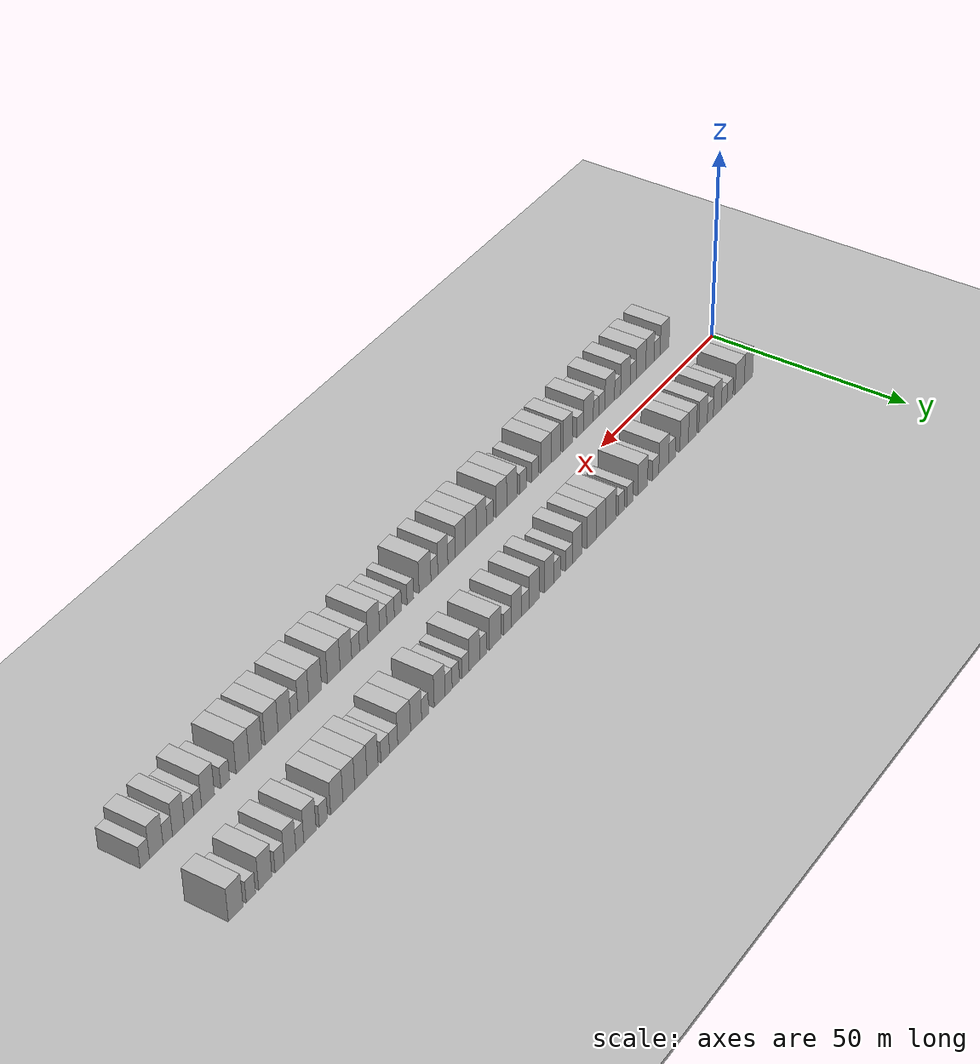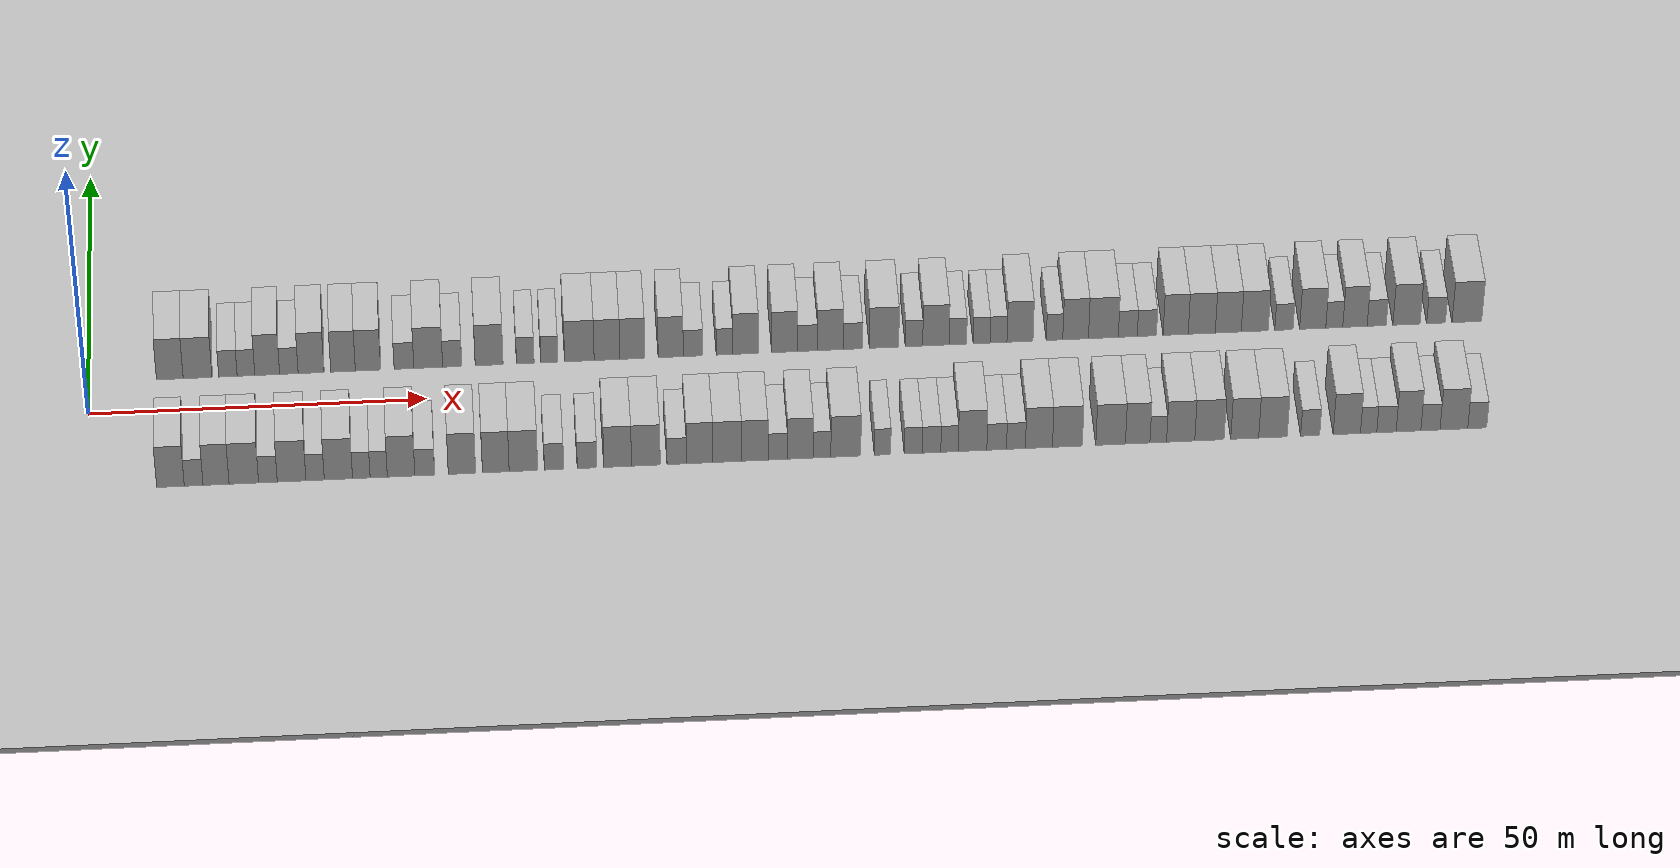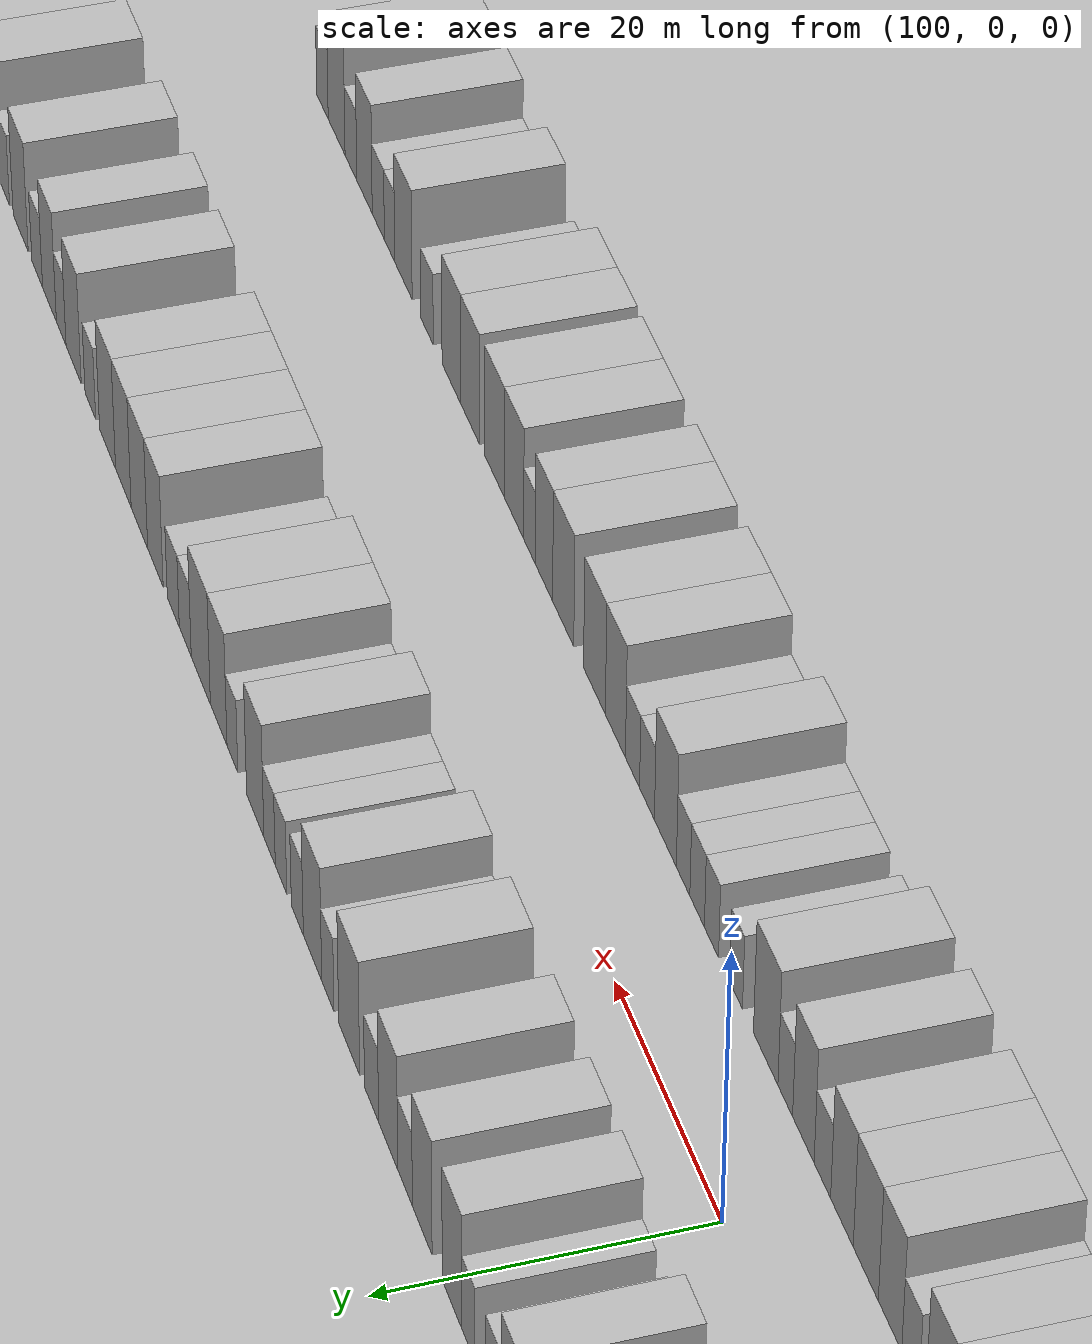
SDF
<?xml version="1.0" encoding="utf-8"?>

<sdf version="1.6">

   <world name="default">

      <gui fullscreen="0">

         <camera name="user_camera">

            <pose>-15 0 4.57585 0 0 0</pose>

            <view_controller>orbit</view_controller>

         </camera>

      </gui>

      <scene>

         <sky>

           <clouds>

             <speed>12</speed>

           </clouds>

         </sky>

         <ambient>0.4 0.4 0.4 1</ambient>

         <background>0.7 0.7 0.7 1</background>

         <shadows>1</shadows>

      </scene>

      <gravity>0 0 -9.8066</gravity>

      <magnetic_field>6e-06 2.3e-05 -4.2e-05</magnetic_field>

      <physics default="0" name="default_physics" type="ode">

         <ode>

            <solver>

               <type>quick</type>

               <iters>10</iters>

               <sor>1.0</sor>

               <use_dynamic_moi_rescaling>0</use_dynamic_moi_rescaling>

            </solver>

            <constraints>

               <cfm>0</cfm>

               <erp>0.2</erp>

               <contact_max_correcting_vel>100</contact_max_correcting_vel>

               <contact_surface_layer>0.001</contact_surface_layer>

            </constraints>

         </ode>

         <max_step_size>0.004</max_step_size>

         <real_time_factor>1</real_time_factor>

         <real_time_update_rate>250</real_time_update_rate>

      </physics>

      <light name="sun" type="directional">

         <cast_shadows>1</cast_shadows>

         <pose>0 0 10 0 0 0</pose>

         <diffuse>0.8 0.8 0.8 1</diffuse>

         <specular>0.2 0.2 0.2 1</specular>

         <attenuation>

            <range>1000</range>

            <constant>0.9</constant>

            <linear>0.01</linear>

            <quadratic>0.001</quadratic>

         </attenuation>

         <direction>-0.5 0.1 -0.9</direction>

      </light>

      <include>

         <name>ground_plane_1</name>

         <uri>model://HANNAS_ground_plane</uri>

         <pose>0 0 0  0 0 0</pose>

      </include>

      <include>

         <name>ground_plane_2</name>

         <uri>model://HANNAS_ground_plane</uri>

         <pose>100 0 0  0 0 0</pose>

      </include>

      <model name="building_1">

         <static>1</static>

         <pose frame="">11.9787 11.0000 0 0.000000 0.000000 1.570796</pose>

         <link name="link">

            <pose frame="">0 0 4.50 0 0 0</pose>

            <collision name="collision">

               <geometry>

                  <box>

                     <size>10.0000 3.9575 9.0000</size>

                  </box>

               </geometry>

               <max_contacts>10</max_contacts>

               <surface>

                  <contact>

                     <ode/>

                  </contact>

                  <bounce/>

                  <friction>

                     <torsional>

                        <ode/>

                     </torsional>

                     <ode/>

                  </friction>

               </surface>

            </collision>

            <visual name="visual">

               <cast_shadows>0</cast_shadows>

               <geometry>

                  <box>

                     <size>10.0000 3.9575 9.0000</size>

                  </box>

               </geometry>

               <material>

                  <script>

                     <uri>model://HANNAS_wall/materials/scripts</uri>

                     <uri>model://HANNAS_wall/materials/textures</uri>

                     <name>vrc/HANNAS_wall</name>

                  </script>

               </material>

            </visual>

            <self_collide>0</self_collide>

            <enable_wind>0</enable_wind>

            <kinematic>0</kinematic>

         </link>

      </model>

      <model name="building_2">

         <static>1</static>

         <pose frame="">16.1000 11.0000 0 0.000000 0.000000 1.570796</pose>

         <link name="link">

            <pose frame="">0 0 4.50 0 0 0</pose>

            <collision name="collision">

               <geometry>

                  <box>

                     <size>10.0000 4.2851 9.0000</size>

                  </box>

               </geometry>

               <max_contacts>10</max_contacts>

               <surface>

                  <contact>

                     <ode/>

                  </contact>

                  <bounce/>

                  <friction>

                     <torsional>

                        <ode/>

                     </torsional>

                     <ode/>

                  </friction>

               </surface>

            </collision>

            <visual name="visual">

               <cast_shadows>0</cast_shadows>

               <geometry>

                  <box>

                     <size>10.0000 4.2851 9.0000</size>

                  </box>

               </geometry>

               <material>

                  <script>

                     <uri>model://HANNAS_wall/materials/scripts</uri>

                     <uri>model://HANNAS_wall/materials/textures</uri>

                     <name>vrc/HANNAS_wall</name>

                  </script>

               </material>

            </visual>

            <self_collide>0</self_collide>

            <enable_wind>0</enable_wind>

            <kinematic>0</kinematic>

         </link>

      </model>

      <model name="building_3">

         <static>1</static>

         <pose frame="">20.6056 11.0000 0 0.000000 0.000000 1.570796</pose>

         <link name="link">

            <pose frame="">0 0 3.00 0 0 0</pose>

            <collision name="collision">

               <geometry>

                  <box>

                     <size>10.0000 2.7262 6.0000</size>

                  </box>

               </geometry>

               <max_contacts>10</max_contacts>

               <surface>

                  <contact>

                     <ode/>

                  </contact>

                  <bounce/>

                  <friction>

                     <torsional>

                        <ode/>

                     </torsional>

                     <ode/>

                  </friction>

               </surface>

            </collision>

            <visual name="visual">

               <cast_shadows>0</cast_shadows>

               <geometry>

                  <box>

                     <size>10.0000 2.7262 6.0000</size>

                  </box>

               </geometry>

               <material>

                  <script>

                     <uri>model://HANNAS_wall/materials/scripts</uri>

                     <uri>model://HANNAS_wall/materials/textures</uri>

                     <name>vrc/HANNAS_wall</name>

                  </script>

               </material>

            </visual>

            <self_collide>0</self_collide>

            <enable_wind>0</enable_wind>

            <kinematic>0</kinematic>

         </link>

      </model>

      <model name="building_4">

         <static>1</static>

         <pose frame="">23.2815 11.0000 0 0.000000 0.000000 1.570796</pose>

         <link name="link">

            <pose frame="">0 0 3.00 0 0 0</pose>

            <collision name="collision">

               <geometry>

                  <box>

                     <size>10.0000 2.6257 6.0000</size>

                  </box>

               </geometry>

               <max_contacts>10</max_contacts>

               <surface>

                  <contact>

                     <ode/>

                  </contact>

                  <bounce/>

                  <friction>

                     <torsional>

                        <ode/>

                     </torsional>

                     <ode/>

                  </friction>

               </surface>

            </collision>

            <visual name="visual">

               <cast_shadows>0</cast_shadows>

               <geometry>

                  <box>

                     <size>10.0000 2.6257 6.0000</size>

                  </box>

               </geometry>

               <material>

                  <script>

                     <uri>model://HANNAS_wall/materials/scripts</uri>

                     <uri>model://HANNAS_wall/materials/textures</uri>

                     <name>vrc/HANNAS_wall</name>

                  </script>

               </material>

            </visual>

            <self_collide>0</self_collide>

            <enable_wind>0</enable_wind>

            <kinematic>0</kinematic>

         </link>

      </model>

      <model name="building_5">

         <static>1</static>

         <pose frame="">26.4376 11.0000 0 0.000000 0.000000 1.570796</pose>

         <link name="link">

            <pose frame="">0 0 4.50 0 0 0</pose>

            <collision name="collision">

               <geometry>

                  <box>

                     <size>10.0000 3.6864 9.0000</size>

                  </box>

               </geometry>

               <max_contacts>10</max_contacts>

               <surface>

                  <contact>

                     <ode/>

                  </contact>

                  <bounce/>

                  <friction>

                     <torsional>

                        <ode/>

                     </torsional>

                     <ode/>

                  </friction>

               </surface>

            </collision>

            <visual name="visual">

               <cast_shadows>0</cast_shadows>

               <geometry>

                  <box>

                     <size>10.0000 3.6864 9.0000</size>

                  </box>

               </geometry>

               <material>

                  <script>

                     <uri>model://HANNAS_wall/materials/scripts</uri>

                     <uri>model://HANNAS_wall/materials/textures</uri>

                     <name>vrc/HANNAS_wall</name>

                  </script>

               </material>

            </visual>

            <self_collide>0</self_collide>

            <enable_wind>0</enable_wind>

            <kinematic>0</kinematic>

         </link>

      </model>

      <model name="building_6">

         <static>1</static>

         <pose frame="">29.6558 11.0000 0 0.000000 0.000000 1.570796</pose>

         <link name="link">

            <pose frame="">0 0 3.00 0 0 0</pose>

            <collision name="collision">

               <geometry>

                  <box>

                     <size>10.0000 2.7500 6.0000</size>

                  </box>

               </geometry>

               <max_contacts>10</max_contacts>

               <surface>

                  <contact>

                     <ode/>

                  </contact>

                  <bounce/>

                  <friction>

                     <torsional>

                        <ode/>

                     </torsional>

                     <ode/>

                  </friction>

               </surface>

            </collision>

            <visual name="visual">

               <cast_shadows>0</cast_shadows>

               <geometry>

                  <box>

                     <size>10.0000 2.7500 6.0000</size>

                  </box>

               </geometry>

               <material>

                  <script>

                     <uri>model://HANNAS_wall/materials/scripts</uri>

                     <uri>model://HANNAS_wall/materials/textures</uri>

                     <name>vrc/HANNAS_wall</name>

                  </script>

               </material>

            </visual>

            <self_collide>0</self_collide>

            <enable_wind>0</enable_wind>

            <kinematic>0</kinematic>

         </link>

      </model>

      <model name="building_7">

         <static>1</static>

         <pose frame="">32.9546 11.0000 0 0.000000 0.000000 1.570796</pose>

         <link name="link">

            <pose frame="">0 0 4.50 0 0 0</pose>

            <collision name="collision">

               <geometry>

                  <box>

                     <size>10.0000 3.8476 9.0000</size>

                  </box>

               </geometry>

               <max_contacts>10</max_contacts>

               <surface>

                  <contact>

                     <ode/>

                  </contact>

                  <bounce/>

                  <friction>

                     <torsional>

                        <ode/>

                     </torsional>

                     <ode/>

                  </friction>

               </surface>

            </collision>

            <visual name="visual">

               <cast_shadows>0</cast_shadows>

               <geometry>

                  <box>

                     <size>10.0000 3.8476 9.0000</size>

                  </box>

               </geometry>

               <material>

                  <script>

                     <uri>model://HANNAS_wall/materials/scripts</uri>

                     <uri>model://HANNAS_wall/materials/textures</uri>

                     <name>vrc/HANNAS_wall</name>

                  </script>

               </material>

            </visual>

            <self_collide>0</self_collide>

            <enable_wind>0</enable_wind>

            <kinematic>0</kinematic>

         </link>

      </model>

      <model name="building_8">

         <static>1</static>

         <pose frame="">37.7054 11.0000 0 0.000000 0.000000 1.570796</pose>

         <link name="link">

            <pose frame="">0 0 4.50 0 0 0</pose>

            <collision name="collision">

               <geometry>

                  <box>

                     <size>10.0000 3.6539 9.0000</size>

                  </box>

               </geometry>

               <max_contacts>10</max_contacts>

               <surface>

                  <contact>

                     <ode/>

                  </contact>

                  <bounce/>

                  <friction>

                     <torsional>

                        <ode/>

                     </torsional>

                     <ode/>

                  </friction>

               </surface>

            </collision>

            <visual name="visual">

               <cast_shadows>0</cast_shadows>

               <geometry>

                  <box>

                     <size>10.0000 3.6539 9.0000</size>

                  </box>

               </geometry>

               <material>

                  <script>

                     <uri>model://HANNAS_wall/materials/scripts</uri>

                     <uri>model://HANNAS_wall/materials/textures</uri>

                     <name>vrc/HANNAS_wall</name>

                  </script>

               </material>

            </visual>

            <self_collide>0</self_collide>

            <enable_wind>0</enable_wind>

            <kinematic>0</kinematic>

         </link>

      </model>

      <model name="building_9">

         <static>1</static>

         <pose frame="">41.4139 11.0000 0 0.000000 0.000000 1.570796</pose>

         <link name="link">

            <pose frame="">0 0 4.50 0 0 0</pose>

            <collision name="collision">

               <geometry>

                  <box>

                     <size>10.0000 3.7632 9.0000</size>

                  </box>

               </geometry>

               <max_contacts>10</max_contacts>

               <surface>

                  <contact>

                     <ode/>

                  </contact>

                  <bounce/>

                  <friction>

                     <torsional>

                        <ode/>

                     </torsional>

                     <ode/>

                  </friction>

               </surface>

            </collision>

            <visual name="visual">

               <cast_shadows>0</cast_shadows>

               <geometry>

                  <box>

                     <size>10.0000 3.7632 9.0000</size>

                  </box>

               </geometry>

               <material>

                  <script>

                     <uri>model://HANNAS_wall/materials/scripts</uri>

                     <uri>model://HANNAS_wall/materials/textures</uri>

                     <name>vrc/HANNAS_wall</name>

                  </script>

               </material>

            </visual>

            <self_collide>0</self_collide>

            <enable_wind>0</enable_wind>

            <kinematic>0</kinematic>

         </link>

      </model>

      <model name="building_10">

         <static>1</static>

         <pose frame="">46.7614 11.0000 0 0.000000 0.000000 1.570796</pose>

         <link name="link">

            <pose frame="">0 0 3.00 0 0 0</pose>

            <collision name="collision">

               <geometry>

                  <box>

                     <size>10.0000 2.9318 6.0000</size>

                  </box>

               </geometry>

               <max_contacts>10</max_contacts>

               <surface>

                  <contact>

                     <ode/>

                  </contact>

                  <bounce/>

                  <friction>

                     <torsional>

                        <ode/>

                     </torsional>

                     <ode/>

                  </friction>

               </surface>

            </collision>

            <visual name="visual">

               <cast_shadows>0</cast_shadows>

               <geometry>

                  <box>

                     <size>10.0000 2.9318 6.0000</size>

                  </box>

               </geometry>

               <material>

                  <script>

                     <uri>model://HANNAS_wall/materials/scripts</uri>

                     <uri>model://HANNAS_wall/materials/textures</uri>

                     <name>vrc/HANNAS_wall</name>

                  </script>

               </material>

            </visual>

            <self_collide>0</self_collide>

            <enable_wind>0</enable_wind>

            <kinematic>0</kinematic>

         </link>

      </model>

      <model name="building_11">

         <static>1</static>

         <pose frame="">50.3703 11.0000 0 0.000000 0.000000 1.570796</pose>

         <link name="link">

            <pose frame="">0 0 4.50 0 0 0</pose>

            <collision name="collision">

               <geometry>

                  <box>

                     <size>10.0000 4.2859 9.0000</size>

                  </box>

               </geometry>

               <max_contacts>10</max_contacts>

               <surface>

                  <contact>

                     <ode/>

                  </contact>

                  <bounce/>

                  <friction>

                     <torsional>

                        <ode/>

                     </torsional>

                     <ode/>

                  </friction>

               </surface>

            </collision>

            <visual name="visual">

               <cast_shadows>0</cast_shadows>

               <geometry>

                  <box>

                     <size>10.0000 4.2859 9.0000</size>

                  </box>

               </geometry>

               <material>

                  <script>

                     <uri>model://HANNAS_wall/materials/scripts</uri>

                     <uri>model://HANNAS_wall/materials/textures</uri>

                     <name>vrc/HANNAS_wall</name>

                  </script>

               </material>

            </visual>

            <self_collide>0</self_collide>

            <enable_wind>0</enable_wind>

            <kinematic>0</kinematic>

         </link>

      </model>

      <model name="building_12">

         <static>1</static>

         <pose frame="">53.9348 11.0000 0 0.000000 0.000000 1.570796</pose>

         <link name="link">

            <pose frame="">0 0 3.00 0 0 0</pose>

            <collision name="collision">

               <geometry>

                  <box>

                     <size>10.0000 2.8431 6.0000</size>

                  </box>

               </geometry>

               <max_contacts>10</max_contacts>

               <surface>

                  <contact>

                     <ode/>

                  </contact>

                  <bounce/>

                  <friction>

                     <torsional>

                        <ode/>

                     </torsional>

                     <ode/>

                  </friction>

               </surface>

            </collision>

            <visual name="visual">

               <cast_shadows>0</cast_shadows>

               <geometry>

                  <box>

                     <size>10.0000 2.8431 6.0000</size>

                  </box>

               </geometry>

               <material>

                  <script>

                     <uri>model://HANNAS_wall/materials/scripts</uri>

                     <uri>model://HANNAS_wall/materials/textures</uri>

                     <name>vrc/HANNAS_wall</name>

                  </script>

               </material>

            </visual>

            <self_collide>0</self_collide>

            <enable_wind>0</enable_wind>

            <kinematic>0</kinematic>

         </link>

      </model>

      <model name="building_13">

         <static>1</static>

         <pose frame="">59.4314 11.0000 0 0.000000 0.000000 1.570796</pose>

         <link name="link">

            <pose frame="">0 0 4.50 0 0 0</pose>

            <collision name="collision">

               <geometry>

                  <box>

                     <size>10.0000 4.1502 9.0000</size>

                  </box>

               </geometry>

               <max_contacts>10</max_contacts>

               <surface>

                  <contact>

                     <ode/>

                  </contact>

                  <bounce/>

                  <friction>

                     <torsional>

                        <ode/>

                     </torsional>

                     <ode/>

                  </friction>

               </surface>

            </collision>

            <visual name="visual">

               <cast_shadows>0</cast_shadows>

               <geometry>

                  <box>

                     <size>10.0000 4.1502 9.0000</size>

                  </box>

               </geometry>

               <material>

                  <script>

                     <uri>model://HANNAS_wall/materials/scripts</uri>

                     <uri>model://HANNAS_wall/materials/textures</uri>

                     <name>vrc/HANNAS_wall</name>

                  </script>

               </material>

            </visual>

            <self_collide>0</self_collide>

            <enable_wind>0</enable_wind>

            <kinematic>0</kinematic>

         </link>

      </model>

      <model name="building_14">

         <static>1</static>

         <pose frame="">64.8158 11.0000 0 0.000000 0.000000 1.570796</pose>

         <link name="link">

            <pose frame="">0 0 3.00 0 0 0</pose>

            <collision name="collision">

               <geometry>

                  <box>

                     <size>10.0000 2.6185 6.0000</size>

                  </box>

               </geometry>

               <max_contacts>10</max_contacts>

               <surface>

                  <contact>

                     <ode/>

                  </contact>

                  <bounce/>

                  <friction>

                     <torsional>

                        <ode/>

                     </torsional>

                     <ode/>

                  </friction>

               </surface>

            </collision>

            <visual name="visual">

               <cast_shadows>0</cast_shadows>

               <geometry>

                  <box>

                     <size>10.0000 2.6185 6.0000</size>

                  </box>

               </geometry>

               <material>

                  <script>

                     <uri>model://HANNAS_wall/materials/scripts</uri>

                     <uri>model://HANNAS_wall/materials/textures</uri>

                     <name>vrc/HANNAS_wall</name>

                  </script>

               </material>

            </visual>

            <self_collide>0</self_collide>

            <enable_wind>0</enable_wind>

            <kinematic>0</kinematic>

         </link>

      </model>

      <model name="building_15">

         <static>1</static>

         <pose frame="">68.3980 11.0000 0 0.000000 0.000000 1.570796</pose>

         <link name="link">

            <pose frame="">0 0 3.00 0 0 0</pose>

            <collision name="collision">

               <geometry>

                  <box>

                     <size>10.0000 2.5458 6.0000</size>

                  </box>

               </geometry>

               <max_contacts>10</max_contacts>

               <surface>

                  <contact>

                     <ode/>

                  </contact>

                  <bounce/>

                  <friction>

                     <torsional>

                        <ode/>

                     </torsional>

                     <ode/>

                  </friction>

               </surface>

            </collision>

            <visual name="visual">

               <cast_shadows>0</cast_shadows>

               <geometry>

                  <box>

                     <size>10.0000 2.5458 6.0000</size>

                  </box>

               </geometry>

               <material>

                  <script>

                     <uri>model://HANNAS_wall/materials/scripts</uri>

                     <uri>model://HANNAS_wall/materials/textures</uri>

                     <name>vrc/HANNAS_wall</name>

                  </script>

               </material>

            </visual>

            <self_collide>0</self_collide>

            <enable_wind>0</enable_wind>

            <kinematic>0</kinematic>

         </link>

      </model>

      <model name="building_16">

         <static>1</static>

         <pose frame="">72.8727 11.0000 0 0.000000 0.000000 1.570796</pose>

         <link name="link">

            <pose frame="">0 0 4.50 0 0 0</pose>

            <collision name="collision">

               <geometry>

                  <box>

                     <size>10.0000 4.4037 9.0000</size>

                  </box>

               </geometry>

               <max_contacts>10</max_contacts>

               <surface>

                  <contact>

                     <ode/>

                  </contact>

                  <bounce/>

                  <friction>

                     <torsional>

                        <ode/>

                     </torsional>

                     <ode/>

                  </friction>

               </surface>

            </collision>

            <visual name="visual">

               <cast_shadows>0</cast_shadows>

               <geometry>

                  <box>

                     <size>10.0000 4.4037 9.0000</size>

                  </box>

               </geometry>

               <material>

                  <script>

                     <uri>model://HANNAS_wall/materials/scripts</uri>

                     <uri>model://HANNAS_wall/materials/textures</uri>

                     <name>vrc/HANNAS_wall</name>

                  </script>

               </material>

            </visual>

            <self_collide>0</self_collide>

            <enable_wind>0</enable_wind>

            <kinematic>0</kinematic>

         </link>

      </model>

      <model name="building_17">

         <static>1</static>

         <pose frame="">76.9914 11.0000 0 0.000000 0.000000 1.570796</pose>

         <link name="link">

            <pose frame="">0 0 4.50 0 0 0</pose>

            <collision name="collision">

               <geometry>

                  <box>

                     <size>10.0000 3.8337 9.0000</size>

                  </box>

               </geometry>

               <max_contacts>10</max_contacts>

               <surface>

                  <contact>

                     <ode/>

                  </contact>

                  <bounce/>

                  <friction>

                     <torsional>

                        <ode/>

                     </torsional>

                     <ode/>

                  </friction>

               </surface>

            </collision>

            <visual name="visual">

               <cast_shadows>0</cast_shadows>

               <geometry>

                  <box>

                     <size>10.0000 3.8337 9.0000</size>

                  </box>

               </geometry>

               <material>

                  <script>

                     <uri>model://HANNAS_wall/materials/scripts</uri>

                     <uri>model://HANNAS_wall/materials/textures</uri>

                     <name>vrc/HANNAS_wall</name>

                  </script>

               </material>

            </visual>

            <self_collide>0</self_collide>

            <enable_wind>0</enable_wind>

            <kinematic>0</kinematic>

         </link>

      </model>

      <model name="building_18">

         <static>1</static>

         <pose frame="">80.7675 11.0000 0 0.000000 0.000000 1.570796</pose>

         <link name="link">

            <pose frame="">0 0 4.50 0 0 0</pose>

            <collision name="collision">

               <geometry>

                  <box>

                     <size>10.0000 3.7185 9.0000</size>

                  </box>

               </geometry>

               <max_contacts>10</max_contacts>

               <surface>

                  <contact>

                     <ode/>

                  </contact>

                  <bounce/>

                  <friction>

                     <torsional>

                        <ode/>

                     </torsional>

                     <ode/>

                  </friction>

               </surface>

            </collision>

            <visual name="visual">

               <cast_shadows>0</cast_shadows>

               <geometry>

                  <box>

                     <size>10.0000 3.7185 9.0000</size>

                  </box>

               </geometry>

               <material>

                  <script>

                     <uri>model://HANNAS_wall/materials/scripts</uri>

                     <uri>model://HANNAS_wall/materials/textures</uri>

                     <name>vrc/HANNAS_wall</name>

                  </script>

               </material>

            </visual>

            <self_collide>0</self_collide>

            <enable_wind>0</enable_wind>

            <kinematic>0</kinematic>

         </link>

      </model>

      <model name="building_19">

         <static>1</static>

         <pose frame="">86.4992 11.0000 0 0.000000 0.000000 1.570796</pose>

         <link name="link">

            <pose frame="">0 0 4.50 0 0 0</pose>

            <collision name="collision">

               <geometry>

                  <box>

                     <size>10.0000 3.7449 9.0000</size>

                  </box>

               </geometry>

               <max_contacts>10</max_contacts>

               <surface>

                  <contact>

                     <ode/>

                  </contact>

                  <bounce/>

                  <friction>

                     <torsional>

                        <ode/>

                     </torsional>

                     <ode/>

                  </friction>

               </surface>

            </collision>

            <visual name="visual">

               <cast_shadows>0</cast_shadows>

               <geometry>

                  <box>

                     <size>10.0000 3.7449 9.0000</size>

                  </box>

               </geometry>

               <material>

                  <script>

                     <uri>model://HANNAS_wall/materials/scripts</uri>

                     <uri>model://HANNAS_wall/materials/textures</uri>

                     <name>vrc/HANNAS_wall</name>

                  </script>

               </material>

            </visual>

            <self_collide>0</self_collide>

            <enable_wind>0</enable_wind>

            <kinematic>0</kinematic>

         </link>

      </model>

      <model name="building_20">

         <static>1</static>

         <pose frame="">89.8305 11.0000 0 0.000000 0.000000 1.570796</pose>

         <link name="link">

            <pose frame="">0 0 3.00 0 0 0</pose>

            <collision name="collision">

               <geometry>

                  <box>

                     <size>10.0000 2.9177 6.0000</size>

                  </box>

               </geometry>

               <max_contacts>10</max_contacts>

               <surface>

                  <contact>

                     <ode/>

                  </contact>

                  <bounce/>

                  <friction>

                     <torsional>

                        <ode/>

                     </torsional>

                     <ode/>

                  </friction>

               </surface>

            </collision>

            <visual name="visual">

               <cast_shadows>0</cast_shadows>

               <geometry>

                  <box>

                     <size>10.0000 2.9177 6.0000</size>

                  </box>

               </geometry>

               <material>

                  <script>

                     <uri>model://HANNAS_wall/materials/scripts</uri>

                     <uri>model://HANNAS_wall/materials/textures</uri>

                     <name>vrc/HANNAS_wall</name>

                  </script>

               </material>

            </visual>

            <self_collide>0</self_collide>

            <enable_wind>0</enable_wind>

            <kinematic>0</kinematic>

         </link>

      </model>

      <model name="building_21">

         <static>1</static>

         <pose frame="">94.5370 11.0000 0 0.000000 0.000000 1.570796</pose>

         <link name="link">

            <pose frame="">0 0 3.00 0 0 0</pose>

            <collision name="collision">

               <geometry>

                  <box>

                     <size>10.0000 2.4954 6.0000</size>

                  </box>

               </geometry>

               <max_contacts>10</max_contacts>

               <surface>

                  <contact>

                     <ode/>

                  </contact>

                  <bounce/>

                  <friction>

                     <torsional>

                        <ode/>

                     </torsional>

                     <ode/>

                  </friction>

               </surface>

            </collision>

            <visual name="visual">

               <cast_shadows>0</cast_shadows>

               <geometry>

                  <box>

                     <size>10.0000 2.4954 6.0000</size>

                  </box>

               </geometry>

               <material>

                  <script>

                     <uri>model://HANNAS_wall/materials/scripts</uri>

                     <uri>model://HANNAS_wall/materials/textures</uri>

                     <name>vrc/HANNAS_wall</name>

                  </script>

               </material>

            </visual>

            <self_collide>0</self_collide>

            <enable_wind>0</enable_wind>

            <kinematic>0</kinematic>

         </link>

      </model>

      <model name="building_22">

         <static>1</static>

         <pose frame="">97.6801 11.0000 0 0.000000 0.000000 1.570796</pose>

         <link name="link">

            <pose frame="">0 0 4.50 0 0 0</pose>

            <collision name="collision">

               <geometry>

                  <box>

                     <size>10.0000 3.7909 9.0000</size>

                  </box>

               </geometry>

               <max_contacts>10</max_contacts>

               <surface>

                  <contact>

                     <ode/>

                  </contact>

                  <bounce/>

                  <friction>

                     <torsional>

                        <ode/>

                     </torsional>

                     <ode/>

                  </friction>

               </surface>

            </collision>

            <visual name="visual">

               <cast_shadows>0</cast_shadows>

               <geometry>

                  <box>

                     <size>10.0000 3.7909 9.0000</size>

                  </box>

               </geometry>

               <material>

                  <script>

                     <uri>model://HANNAS_wall/materials/scripts</uri>

                     <uri>model://HANNAS_wall/materials/textures</uri>

                     <name>vrc/HANNAS_wall</name>

                  </script>

               </material>

            </visual>

            <self_collide>0</self_collide>

            <enable_wind>0</enable_wind>

            <kinematic>0</kinematic>

         </link>

      </model>

      <model name="building_23">

         <static>1</static>

         <pose frame="">103.5225 11.0000 0 0.000000 0.000000 1.570796</pose>

         <link name="link">

            <pose frame="">0 0 4.50 0 0 0</pose>

            <collision name="collision">

               <geometry>

                  <box>

                     <size>10.0000 3.8938 9.0000</size>

                  </box>

               </geometry>

               <max_contacts>10</max_contacts>

               <surface>

                  <contact>

                     <ode/>

                  </contact>

                  <bounce/>

                  <friction>

                     <torsional>

                        <ode/>

                     </torsional>

                     <ode/>

                  </friction>

               </surface>

            </collision>

            <visual name="visual">

               <cast_shadows>0</cast_shadows>

               <geometry>

                  <box>

                     <size>10.0000 3.8938 9.0000</size>

                  </box>

               </geometry>

               <material>

                  <script>

                     <uri>model://HANNAS_wall/materials/scripts</uri>

                     <uri>model://HANNAS_wall/materials/textures</uri>

                     <name>vrc/HANNAS_wall</name>

                  </script>

               </material>

            </visual>

            <self_collide>0</self_collide>

            <enable_wind>0</enable_wind>

            <kinematic>0</kinematic>

         </link>

      </model>

      <model name="building_24">

         <static>1</static>

         <pose frame="">106.9337 11.0000 0 0.000000 0.000000 1.570796</pose>

         <link name="link">

            <pose frame="">0 0 3.00 0 0 0</pose>

            <collision name="collision">

               <geometry>

                  <box>

                     <size>10.0000 2.9285 6.0000</size>

                  </box>

               </geometry>

               <max_contacts>10</max_contacts>

               <surface>

                  <contact>

                     <ode/>

                  </contact>

                  <bounce/>

                  <friction>

                     <torsional>

                        <ode/>

                     </torsional>

                     <ode/>

                  </friction>

               </surface>

            </collision>

            <visual name="visual">

               <cast_shadows>0</cast_shadows>

               <geometry>

                  <box>

                     <size>10.0000 2.9285 6.0000</size>

                  </box>

               </geometry>

               <material>

                  <script>

                     <uri>model://HANNAS_wall/materials/scripts</uri>

                     <uri>model://HANNAS_wall/materials/textures</uri>

                     <name>vrc/HANNAS_wall</name>

                  </script>

               </material>

            </visual>

            <self_collide>0</self_collide>

            <enable_wind>0</enable_wind>

            <kinematic>0</kinematic>

         </link>

      </model>

      <model name="building_25">

         <static>1</static>

         <pose frame="">110.3407 11.0000 0 0.000000 0.000000 1.570796</pose>

         <link name="link">

            <pose frame="">0 0 4.50 0 0 0</pose>

            <collision name="collision">

               <geometry>

                  <box>

                     <size>10.0000 3.8856 9.0000</size>

                  </box>

               </geometry>

               <max_contacts>10</max_contacts>

               <surface>

                  <contact>

                     <ode/>

                  </contact>

                  <bounce/>

                  <friction>

                     <torsional>

                        <ode/>

                     </torsional>

                     <ode/>

                  </friction>

               </surface>

            </collision>

            <visual name="visual">

               <cast_shadows>0</cast_shadows>

               <geometry>

                  <box>

                     <size>10.0000 3.8856 9.0000</size>

                  </box>

               </geometry>

               <material>

                  <script>

                     <uri>model://HANNAS_wall/materials/scripts</uri>

                     <uri>model://HANNAS_wall/materials/textures</uri>

                     <name>vrc/HANNAS_wall</name>

                  </script>

               </material>

            </visual>

            <self_collide>0</self_collide>

            <enable_wind>0</enable_wind>

            <kinematic>0</kinematic>

         </link>

      </model>

      <model name="building_26">

         <static>1</static>

         <pose frame="">113.7288 11.0000 0 0.000000 0.000000 1.570796</pose>

         <link name="link">

            <pose frame="">0 0 3.00 0 0 0</pose>

            <collision name="collision">

               <geometry>

                  <box>

                     <size>10.0000 2.8907 6.0000</size>

                  </box>

               </geometry>

               <max_contacts>10</max_contacts>

               <surface>

                  <contact>

                     <ode/>

                  </contact>

                  <bounce/>

                  <friction>

                     <torsional>

                        <ode/>

                     </torsional>

                     <ode/>

                  </friction>

               </surface>

            </collision>

            <visual name="visual">

               <cast_shadows>0</cast_shadows>

               <geometry>

                  <box>

                     <size>10.0000 2.8907 6.0000</size>

                  </box>

               </geometry>

               <material>

                  <script>

                     <uri>model://HANNAS_wall/materials/scripts</uri>

                     <uri>model://HANNAS_wall/materials/textures</uri>

                     <name>vrc/HANNAS_wall</name>

                  </script>

               </material>

            </visual>

            <self_collide>0</self_collide>

            <enable_wind>0</enable_wind>

            <kinematic>0</kinematic>

         </link>

      </model>

      <model name="building_27">

         <static>1</static>

         <pose frame="">118.3652 11.0000 0 0.000000 0.000000 1.570796</pose>

         <link name="link">

            <pose frame="">0 0 4.50 0 0 0</pose>

            <collision name="collision">

               <geometry>

                  <box>

                     <size>10.0000 4.3821 9.0000</size>

                  </box>

               </geometry>

               <max_contacts>10</max_contacts>

               <surface>

                  <contact>

                     <ode/>

                  </contact>

                  <bounce/>

                  <friction>

                     <torsional>

                        <ode/>

                     </torsional>

                     <ode/>

                  </friction>

               </surface>

            </collision>

            <visual name="visual">

               <cast_shadows>0</cast_shadows>

               <geometry>

                  <box>

                     <size>10.0000 4.3821 9.0000</size>

                  </box>

               </geometry>

               <material>

                  <script>

                     <uri>model://HANNAS_wall/materials/scripts</uri>

                     <uri>model://HANNAS_wall/materials/textures</uri>

                     <name>vrc/HANNAS_wall</name>

                  </script>

               </material>

            </visual>

            <self_collide>0</self_collide>

            <enable_wind>0</enable_wind>

            <kinematic>0</kinematic>

         </link>

      </model>

      <model name="building_28">

         <static>1</static>

         <pose frame="">122.8509 11.0000 0 0.000000 0.000000 1.570796</pose>

         <link name="link">

            <pose frame="">0 0 3.00 0 0 0</pose>

            <collision name="collision">

               <geometry>

                  <box>

                     <size>10.0000 2.5893 6.0000</size>

                  </box>

               </geometry>

               <max_contacts>10</max_contacts>

               <surface>

                  <contact>

                     <ode/>

                  </contact>

                  <bounce/>

                  <friction>

                     <torsional>

                        <ode/>

                     </torsional>

                     <ode/>

                  </friction>

               </surface>

            </collision>

            <visual name="visual">

               <cast_shadows>0</cast_shadows>

               <geometry>

                  <box>

                     <size>10.0000 2.5893 6.0000</size>

                  </box>

               </geometry>

               <material>

                  <script>

                     <uri>model://HANNAS_wall/materials/scripts</uri>

                     <uri>model://HANNAS_wall/materials/textures</uri>

                     <name>vrc/HANNAS_wall</name>

                  </script>

               </material>

            </visual>

            <self_collide>0</self_collide>

            <enable_wind>0</enable_wind>

            <kinematic>0</kinematic>

         </link>

      </model>

      <model name="building_29">

         <static>1</static>

         <pose frame="">126.1246 11.0000 0 0.000000 0.000000 1.570796</pose>

         <link name="link">

            <pose frame="">0 0 4.50 0 0 0</pose>

            <collision name="collision">

               <geometry>

                  <box>

                     <size>10.0000 3.9582 9.0000</size>

                  </box>

               </geometry>

               <max_contacts>10</max_contacts>

               <surface>

                  <contact>

                     <ode/>

                  </contact>

                  <bounce/>

                  <friction>

                     <torsional>

                        <ode/>

                     </torsional>

                     <ode/>

                  </friction>

               </surface>

            </collision>

            <visual name="visual">

               <cast_shadows>0</cast_shadows>

               <geometry>

                  <box>

                     <size>10.0000 3.9582 9.0000</size>

                  </box>

               </geometry>

               <material>

                  <script>

                     <uri>model://HANNAS_wall/materials/scripts</uri>

                     <uri>model://HANNAS_wall/materials/textures</uri>

                     <name>vrc/HANNAS_wall</name>

                  </script>

               </material>

            </visual>

            <self_collide>0</self_collide>

            <enable_wind>0</enable_wind>

            <kinematic>0</kinematic>

         </link>

      </model>

      <model name="building_30">

         <static>1</static>

         <pose frame="">129.4086 11.0000 0 0.000000 0.000000 1.570796</pose>

         <link name="link">

            <pose frame="">0 0 3.00 0 0 0</pose>

            <collision name="collision">

               <geometry>

                  <box>

                     <size>10.0000 2.6097 6.0000</size>

                  </box>

               </geometry>

               <max_contacts>10</max_contacts>

               <surface>

                  <contact>

                     <ode/>

                  </contact>

                  <bounce/>

                  <friction>

                     <torsional>

                        <ode/>

                     </torsional>

                     <ode/>

                  </friction>

               </surface>

            </collision>

            <visual name="visual">

               <cast_shadows>0</cast_shadows>

               <geometry>

                  <box>

                     <size>10.0000 2.6097 6.0000</size>

                  </box>

               </geometry>

               <material>

                  <script>

                     <uri>model://HANNAS_wall/materials/scripts</uri>

                     <uri>model://HANNAS_wall/materials/textures</uri>

                     <name>vrc/HANNAS_wall</name>

                  </script>

               </material>

            </visual>

            <self_collide>0</self_collide>

            <enable_wind>0</enable_wind>

            <kinematic>0</kinematic>

         </link>

      </model>

      <model name="building_31">

         <static>1</static>

         <pose frame="">132.9800 11.0000 0 0.000000 0.000000 1.570796</pose>

         <link name="link">

            <pose frame="">0 0 3.00 0 0 0</pose>

            <collision name="collision">

               <geometry>

                  <box>

                     <size>10.0000 2.5331 6.0000</size>

                  </box>

               </geometry>

               <max_contacts>10</max_contacts>

               <surface>

                  <contact>

                     <ode/>

                  </contact>

                  <bounce/>

                  <friction>

                     <torsional>

                        <ode/>

                     </torsional>

                     <ode/>

                  </friction>

               </surface>

            </collision>

            <visual name="visual">

               <cast_shadows>0</cast_shadows>

               <geometry>

                  <box>

                     <size>10.0000 2.5331 6.0000</size>

                  </box>

               </geometry>

               <material>

                  <script>

                     <uri>model://HANNAS_wall/materials/scripts</uri>

                     <uri>model://HANNAS_wall/materials/textures</uri>

                     <name>vrc/HANNAS_wall</name>

                  </script>

               </material>

            </visual>

            <self_collide>0</self_collide>

            <enable_wind>0</enable_wind>

            <kinematic>0</kinematic>

         </link>

      </model>

      <model name="building_32">

         <static>1</static>

         <pose frame="">135.5073 11.0000 0 0.000000 0.000000 1.570796</pose>

         <link name="link">

            <pose frame="">0 0 3.00 0 0 0</pose>

            <collision name="collision">

               <geometry>

                  <box>

                     <size>10.0000 2.5216 6.0000</size>

                  </box>

               </geometry>

               <max_contacts>10</max_contacts>

               <surface>

                  <contact>

                     <ode/>

                  </contact>

                  <bounce/>

                  <friction>

                     <torsional>

                        <ode/>

                     </torsional>

                     <ode/>

                  </friction>

               </surface>

            </collision>

            <visual name="visual">

               <cast_shadows>0</cast_shadows>

               <geometry>

                  <box>

                     <size>10.0000 2.5216 6.0000</size>

                  </box>

               </geometry>

               <material>

                  <script>

                     <uri>model://HANNAS_wall/materials/scripts</uri>

                     <uri>model://HANNAS_wall/materials/textures</uri>

                     <name>vrc/HANNAS_wall</name>

                  </script>

               </material>

            </visual>

            <self_collide>0</self_collide>

            <enable_wind>0</enable_wind>

            <kinematic>0</kinematic>

         </link>

      </model>

      <model name="building_33">

         <static>1</static>

         <pose frame="">138.7132 11.0000 0 0.000000 0.000000 1.570796</pose>

         <link name="link">

            <pose frame="">0 0 4.50 0 0 0</pose>

            <collision name="collision">

               <geometry>

                  <box>

                     <size>10.0000 3.8902 9.0000</size>

                  </box>

               </geometry>

               <max_contacts>10</max_contacts>

               <surface>

                  <contact>

                     <ode/>

                  </contact>

                  <bounce/>

                  <friction>

                     <torsional>

                        <ode/>

                     </torsional>

                     <ode/>

                  </friction>

               </surface>

            </collision>

            <visual name="visual">

               <cast_shadows>0</cast_shadows>

               <geometry>

                  <box>

                     <size>10.0000 3.8902 9.0000</size>

                  </box>

               </geometry>

               <material>

                  <script>

                     <uri>model://HANNAS_wall/materials/scripts</uri>

                     <uri>model://HANNAS_wall/materials/textures</uri>

                     <name>vrc/HANNAS_wall</name>

                  </script>

               </material>

            </visual>

            <self_collide>0</self_collide>

            <enable_wind>0</enable_wind>

            <kinematic>0</kinematic>

         </link>

      </model>

      <model name="building_34">

         <static>1</static>

         <pose frame="">143.8912 11.0000 0 0.000000 0.000000 1.570796</pose>

         <link name="link">

            <pose frame="">0 0 3.00 0 0 0</pose>

            <collision name="collision">

               <geometry>

                  <box>

                     <size>10.0000 2.4657 6.0000</size>

                  </box>

               </geometry>

               <max_contacts>10</max_contacts>

               <surface>

                  <contact>

                     <ode/>

                  </contact>

                  <bounce/>

                  <friction>

                     <torsional>

                        <ode/>

                     </torsional>

                     <ode/>

                  </friction>

               </surface>

            </collision>

            <visual name="visual">

               <cast_shadows>0</cast_shadows>

               <geometry>

                  <box>

                     <size>10.0000 2.4657 6.0000</size>

                  </box>

               </geometry>

               <material>

                  <script>

                     <uri>model://HANNAS_wall/materials/scripts</uri>

                     <uri>model://HANNAS_wall/materials/textures</uri>

                     <name>vrc/HANNAS_wall</name>

                  </script>

               </material>

            </visual>

            <self_collide>0</self_collide>

            <enable_wind>0</enable_wind>

            <kinematic>0</kinematic>

         </link>

      </model>

      <model name="building_35">

         <static>1</static>

         <pose frame="">147.0525 11.0000 0 0.000000 0.000000 1.570796</pose>

         <link name="link">

            <pose frame="">0 0 4.50 0 0 0</pose>

            <collision name="collision">

               <geometry>

                  <box>

                     <size>10.0000 3.8570 9.0000</size>

                  </box>

               </geometry>

               <max_contacts>10</max_contacts>

               <surface>

                  <contact>

                     <ode/>

                  </contact>

                  <bounce/>

                  <friction>

                     <torsional>

                        <ode/>

                     </torsional>

                     <ode/>

                  </friction>

               </surface>

            </collision>

            <visual name="visual">

               <cast_shadows>0</cast_shadows>

               <geometry>

                  <box>

                     <size>10.0000 3.8570 9.0000</size>

                  </box>

               </geometry>

               <material>

                  <script>

                     <uri>model://HANNAS_wall/materials/scripts</uri>

                     <uri>model://HANNAS_wall/materials/textures</uri>

                     <name>vrc/HANNAS_wall</name>

                  </script>

               </material>

            </visual>

            <self_collide>0</self_collide>

            <enable_wind>0</enable_wind>

            <kinematic>0</kinematic>

         </link>

      </model>

      <model name="building_36">

         <static>1</static>

         <pose frame="">151.2220 11.0000 0 0.000000 0.000000 1.570796</pose>

         <link name="link">

            <pose frame="">0 0 4.50 0 0 0</pose>

            <collision name="collision">

               <geometry>

                  <box>

                     <size>10.0000 4.4820 9.0000</size>

                  </box>

               </geometry>

               <max_contacts>10</max_contacts>

               <surface>

                  <contact>

                     <ode/>

                  </contact>

                  <bounce/>

                  <friction>

                     <torsional>

                        <ode/>

                     </torsional>

                     <ode/>

                  </friction>

               </surface>

            </collision>

            <visual name="visual">

               <cast_shadows>0</cast_shadows>

               <geometry>

                  <box>

                     <size>10.0000 4.4820 9.0000</size>

                  </box>

               </geometry>

               <material>

                  <script>

                     <uri>model://HANNAS_wall/materials/scripts</uri>

                     <uri>model://HANNAS_wall/materials/textures</uri>

                     <name>vrc/HANNAS_wall</name>

                  </script>

               </material>

            </visual>

            <self_collide>0</self_collide>

            <enable_wind>0</enable_wind>

            <kinematic>0</kinematic>

         </link>

      </model>

      <model name="building_37">

         <static>1</static>

         <pose frame="">154.8846 11.0000 0 0.000000 0.000000 1.570796</pose>

         <link name="link">

            <pose frame="">0 0 3.00 0 0 0</pose>

            <collision name="collision">

               <geometry>

                  <box>

                     <size>10.0000 2.8432 6.0000</size>

                  </box>

               </geometry>

               <max_contacts>10</max_contacts>

               <surface>

                  <contact>

                     <ode/>

                  </contact>

                  <bounce/>

                  <friction>

                     <torsional>

                        <ode/>

                     </torsional>

                     <ode/>

                  </friction>

               </surface>

            </collision>

            <visual name="visual">

               <cast_shadows>0</cast_shadows>

               <geometry>

                  <box>

                     <size>10.0000 2.8432 6.0000</size>

                  </box>

               </geometry>

               <material>

                  <script>

                     <uri>model://HANNAS_wall/materials/scripts</uri>

                     <uri>model://HANNAS_wall/materials/textures</uri>

                     <name>vrc/HANNAS_wall</name>

                  </script>

               </material>

            </visual>

            <self_collide>0</self_collide>

            <enable_wind>0</enable_wind>

            <kinematic>0</kinematic>

         </link>

      </model>

      <model name="building_38">

         <static>1</static>

         <pose frame="">157.7415 11.0000 0 0.000000 0.000000 1.570796</pose>

         <link name="link">

            <pose frame="">0 0 3.00 0 0 0</pose>

            <collision name="collision">

               <geometry>

                  <box>

                     <size>10.0000 2.8707 6.0000</size>

                  </box>

               </geometry>

               <max_contacts>10</max_contacts>

               <surface>

                  <contact>

                     <ode/>

                  </contact>

                  <bounce/>

                  <friction>

                     <torsional>

                        <ode/>

                     </torsional>

                     <ode/>

                  </friction>

               </surface>

            </collision>

            <visual name="visual">

               <cast_shadows>0</cast_shadows>

               <geometry>

                  <box>

                     <size>10.0000 2.8707 6.0000</size>

                  </box>

               </geometry>

               <material>

                  <script>

                     <uri>model://HANNAS_wall/materials/scripts</uri>

                     <uri>model://HANNAS_wall/materials/textures</uri>

                     <name>vrc/HANNAS_wall</name>

                  </script>

               </material>

            </visual>

            <self_collide>0</self_collide>

            <enable_wind>0</enable_wind>

            <kinematic>0</kinematic>

         </link>

      </model>

      <model name="building_39">

         <static>1</static>

         <pose frame="">162.0608 11.0000 0 0.000000 0.000000 1.570796</pose>

         <link name="link">

            <pose frame="">0 0 4.50 0 0 0</pose>

            <collision name="collision">

               <geometry>

                  <box>

                     <size>10.0000 3.7678 9.0000</size>

                  </box>

               </geometry>

               <max_contacts>10</max_contacts>

               <surface>

                  <contact>

                     <ode/>

                  </contact>

                  <bounce/>

                  <friction>

                     <torsional>

                        <ode/>

                     </torsional>

                     <ode/>

                  </friction>

               </surface>

            </collision>

            <visual name="visual">

               <cast_shadows>0</cast_shadows>

               <geometry>

                  <box>

                     <size>10.0000 3.7678 9.0000</size>

                  </box>

               </geometry>

               <material>

                  <script>

                     <uri>model://HANNAS_wall/materials/scripts</uri>

                     <uri>model://HANNAS_wall/materials/textures</uri>

                     <name>vrc/HANNAS_wall</name>

                  </script>

               </material>

            </visual>

            <self_collide>0</self_collide>

            <enable_wind>0</enable_wind>

            <kinematic>0</kinematic>

         </link>

      </model>

      <model name="building_40">

         <static>1</static>

         <pose frame="">165.9803 11.0000 0 0.000000 0.000000 1.570796</pose>

         <link name="link">

            <pose frame="">0 0 4.50 0 0 0</pose>

            <collision name="collision">

               <geometry>

                  <box>

                     <size>10.0000 4.0713 9.0000</size>

                  </box>

               </geometry>

               <max_contacts>10</max_contacts>

               <surface>

                  <contact>

                     <ode/>

                  </contact>

                  <bounce/>

                  <friction>

                     <torsional>

                        <ode/>

                     </torsional>

                     <ode/>

                  </friction>

               </surface>

            </collision>

            <visual name="visual">

               <cast_shadows>0</cast_shadows>

               <geometry>

                  <box>

                     <size>10.0000 4.0713 9.0000</size>

                  </box>

               </geometry>

               <material>

                  <script>

                     <uri>model://HANNAS_wall/materials/scripts</uri>

                     <uri>model://HANNAS_wall/materials/textures</uri>

                     <name>vrc/HANNAS_wall</name>

                  </script>

               </material>

            </visual>

            <self_collide>0</self_collide>

            <enable_wind>0</enable_wind>

            <kinematic>0</kinematic>

         </link>

      </model>

      <model name="building_41">

         <static>1</static>

         <pose frame="">169.9663 11.0000 0 0.000000 0.000000 1.570796</pose>

         <link name="link">

            <pose frame="">0 0 4.50 0 0 0</pose>

            <collision name="collision">

               <geometry>

                  <box>

                     <size>10.0000 3.9006 9.0000</size>

                  </box>

               </geometry>

               <max_contacts>10</max_contacts>

               <surface>

                  <contact>

                     <ode/>

                  </contact>

                  <bounce/>

                  <friction>

                     <torsional>

                        <ode/>

                     </torsional>

                     <ode/>

                  </friction>

               </surface>

            </collision>

            <visual name="visual">

               <cast_shadows>0</cast_shadows>

               <geometry>

                  <box>

                     <size>10.0000 3.9006 9.0000</size>

                  </box>

               </geometry>

               <material>

                  <script>

                     <uri>model://HANNAS_wall/materials/scripts</uri>

                     <uri>model://HANNAS_wall/materials/textures</uri>

                     <name>vrc/HANNAS_wall</name>

                  </script>

               </material>

            </visual>

            <self_collide>0</self_collide>

            <enable_wind>0</enable_wind>

            <kinematic>0</kinematic>

         </link>

      </model>

      <model name="building_42">

         <static>1</static>

         <pose frame="">173.9365 11.0000 0 0.000000 0.000000 1.570796</pose>

         <link name="link">

            <pose frame="">0 0 4.50 0 0 0</pose>

            <collision name="collision">

               <geometry>

                  <box>

                     <size>10.0000 4.0397 9.0000</size>

                  </box>

               </geometry>

               <max_contacts>10</max_contacts>

               <surface>

                  <contact>

                     <ode/>

                  </contact>

                  <bounce/>

                  <friction>

                     <torsional>

                        <ode/>

                     </torsional>

                     <ode/>

                  </friction>

               </surface>

            </collision>

            <visual name="visual">

               <cast_shadows>0</cast_shadows>

               <geometry>

                  <box>

                     <size>10.0000 4.0397 9.0000</size>

                  </box>

               </geometry>

               <material>

                  <script>

                     <uri>model://HANNAS_wall/materials/scripts</uri>

                     <uri>model://HANNAS_wall/materials/textures</uri>

                     <name>vrc/HANNAS_wall</name>

                  </script>

               </material>

            </visual>

            <self_collide>0</self_collide>

            <enable_wind>0</enable_wind>

            <kinematic>0</kinematic>

         </link>

      </model>

      <model name="building_43">

         <static>1</static>

         <pose frame="">178.3204 11.0000 0 0.000000 0.000000 1.570796</pose>

         <link name="link">

            <pose frame="">0 0 3.00 0 0 0</pose>

            <collision name="collision">

               <geometry>

                  <box>

                     <size>10.0000 2.7282 6.0000</size>

                  </box>

               </geometry>

               <max_contacts>10</max_contacts>

               <surface>

                  <contact>

                     <ode/>

                  </contact>

                  <bounce/>

                  <friction>

                     <torsional>

                        <ode/>

                     </torsional>

                     <ode/>

                  </friction>

               </surface>

            </collision>

            <visual name="visual">

               <cast_shadows>0</cast_shadows>

               <geometry>

                  <box>

                     <size>10.0000 2.7282 6.0000</size>

                  </box>

               </geometry>

               <material>

                  <script>

                     <uri>model://HANNAS_wall/materials/scripts</uri>

                     <uri>model://HANNAS_wall/materials/textures</uri>

                     <name>vrc/HANNAS_wall</name>

                  </script>

               </material>

            </visual>

            <self_collide>0</self_collide>

            <enable_wind>0</enable_wind>

            <kinematic>0</kinematic>

         </link>

      </model>

      <model name="building_44">

         <static>1</static>

         <pose frame="">182.6560 11.0000 0 0.000000 0.000000 1.570796</pose>

         <link name="link">

            <pose frame="">0 0 4.50 0 0 0</pose>

            <collision name="collision">

               <geometry>

                  <box>

                     <size>10.0000 3.9429 9.0000</size>

                  </box>

               </geometry>

               <max_contacts>10</max_contacts>

               <surface>

                  <contact>

                     <ode/>

                  </contact>

                  <bounce/>

                  <friction>

                     <torsional>

                        <ode/>

                     </torsional>

                     <ode/>

                  </friction>

               </surface>

            </collision>

            <visual name="visual">

               <cast_shadows>0</cast_shadows>

               <geometry>

                  <box>

                     <size>10.0000 3.9429 9.0000</size>

                  </box>

               </geometry>

               <material>

                  <script>

                     <uri>model://HANNAS_wall/materials/scripts</uri>

                     <uri>model://HANNAS_wall/materials/textures</uri>

                     <name>vrc/HANNAS_wall</name>

                  </script>

               </material>

            </visual>

            <self_collide>0</self_collide>

            <enable_wind>0</enable_wind>

            <kinematic>0</kinematic>

         </link>

      </model>

      <model name="building_45">

         <static>1</static>

         <pose frame="">185.9031 11.0000 0 0.000000 0.000000 1.570796</pose>

         <link name="link">

            <pose frame="">0 0 3.00 0 0 0</pose>

            <collision name="collision">

               <geometry>

                  <box>

                     <size>10.0000 2.5512 6.0000</size>

                  </box>

               </geometry>

               <max_contacts>10</max_contacts>

               <surface>

                  <contact>

                     <ode/>

                  </contact>

                  <bounce/>

                  <friction>

                     <torsional>

                        <ode/>

                     </torsional>

                     <ode/>

                  </friction>

               </surface>

            </collision>

            <visual name="visual">

               <cast_shadows>0</cast_shadows>

               <geometry>

                  <box>

                     <size>10.0000 2.5512 6.0000</size>

                  </box>

               </geometry>

               <material>

                  <script>

                     <uri>model://HANNAS_wall/materials/scripts</uri>

                     <uri>model://HANNAS_wall/materials/textures</uri>

                     <name>vrc/HANNAS_wall</name>

                  </script>

               </material>

            </visual>

            <self_collide>0</self_collide>

            <enable_wind>0</enable_wind>

            <kinematic>0</kinematic>

         </link>

      </model>

      <model name="building_46">

         <static>1</static>

         <pose frame="">189.0134 11.0000 0 0.000000 0.000000 1.570796</pose>

         <link name="link">

            <pose frame="">0 0 4.50 0 0 0</pose>

            <collision name="collision">

               <geometry>

                  <box>

                     <size>10.0000 3.6694 9.0000</size>

                  </box>

               </geometry>

               <max_contacts>10</max_contacts>

               <surface>

                  <contact>

                     <ode/>

                  </contact>

                  <bounce/>

                  <friction>

                     <torsional>

                        <ode/>

                     </torsional>

                     <ode/>

                  </friction>

               </surface>

            </collision>

            <visual name="visual">

               <cast_shadows>0</cast_shadows>

               <geometry>

                  <box>

                     <size>10.0000 3.6694 9.0000</size>

                  </box>

               </geometry>

               <material>

                  <script>

                     <uri>model://HANNAS_wall/materials/scripts</uri>

                     <uri>model://HANNAS_wall/materials/textures</uri>

                     <name>vrc/HANNAS_wall</name>

                  </script>

               </material>

            </visual>

            <self_collide>0</self_collide>

            <enable_wind>0</enable_wind>

            <kinematic>0</kinematic>

         </link>

      </model>

      <model name="building_47">

         <static>1</static>

         <pose frame="">192.2828 11.0000 0 0.000000 0.000000 1.570796</pose>

         <link name="link">

            <pose frame="">0 0 3.00 0 0 0</pose>

            <collision name="collision">

               <geometry>

                  <box>

                     <size>10.0000 2.8692 6.0000</size>

                  </box>

               </geometry>

               <max_contacts>10</max_contacts>

               <surface>

                  <contact>

                     <ode/>

                  </contact>

                  <bounce/>

                  <friction>

                     <torsional>

                        <ode/>

                     </torsional>

                     <ode/>

                  </friction>

               </surface>

            </collision>

            <visual name="visual">

               <cast_shadows>0</cast_shadows>

               <geometry>

                  <box>

                     <size>10.0000 2.8692 6.0000</size>

                  </box>

               </geometry>

               <material>

                  <script>

                     <uri>model://HANNAS_wall/materials/scripts</uri>

                     <uri>model://HANNAS_wall/materials/textures</uri>

                     <name>vrc/HANNAS_wall</name>

                  </script>

               </material>

            </visual>

            <self_collide>0</self_collide>

            <enable_wind>0</enable_wind>

            <kinematic>0</kinematic>

         </link>

      </model>

      <model name="building_48">

         <static>1</static>

         <pose frame="">196.7626 11.0000 0 0.000000 0.000000 1.570796</pose>

         <link name="link">

            <pose frame="">0 0 4.50 0 0 0</pose>

            <collision name="collision">

               <geometry>

                  <box>

                     <size>10.0000 4.0905 9.0000</size>

                  </box>

               </geometry>

               <max_contacts>10</max_contacts>

               <surface>

                  <contact>

                     <ode/>

                  </contact>

                  <bounce/>

                  <friction>

                     <torsional>

                        <ode/>

                     </torsional>

                     <ode/>

                  </friction>

               </surface>

            </collision>

            <visual name="visual">

               <cast_shadows>0</cast_shadows>

               <geometry>

                  <box>

                     <size>10.0000 4.0905 9.0000</size>

                  </box>

               </geometry>

               <material>

                  <script>

                     <uri>model://HANNAS_wall/materials/scripts</uri>

                     <uri>model://HANNAS_wall/materials/textures</uri>

                     <name>vrc/HANNAS_wall</name>

                  </script>

               </material>

            </visual>

            <self_collide>0</self_collide>

            <enable_wind>0</enable_wind>

            <kinematic>0</kinematic>

         </link>

      </model>

      <model name="building_49">

         <static>1</static>

         <pose frame="">201.2171 11.0000 0 0.000000 0.000000 1.570796</pose>

         <link name="link">

            <pose frame="">0 0 3.00 0 0 0</pose>

            <collision name="collision">

               <geometry>

                  <box>

                     <size>10.0000 2.8185 6.0000</size>

                  </box>

               </geometry>

               <max_contacts>10</max_contacts>

               <surface>

                  <contact>

                     <ode/>

                  </contact>

                  <bounce/>

                  <friction>

                     <torsional>

                        <ode/>

                     </torsional>

                     <ode/>

                  </friction>

               </surface>

            </collision>

            <visual name="visual">

               <cast_shadows>0</cast_shadows>

               <geometry>

                  <box>

                     <size>10.0000 2.8185 6.0000</size>

                  </box>

               </geometry>

               <material>

                  <script>

                     <uri>model://HANNAS_wall/materials/scripts</uri>

                     <uri>model://HANNAS_wall/materials/textures</uri>

                     <name>vrc/HANNAS_wall</name>

                  </script>

               </material>

            </visual>

            <self_collide>0</self_collide>

            <enable_wind>0</enable_wind>

            <kinematic>0</kinematic>

         </link>

      </model>

      <model name="building_50">

         <static>1</static>

         <pose frame="">205.8533 11.0000 0 0.000000 0.000000 1.570796</pose>

         <link name="link">

            <pose frame="">0 0 4.50 0 0 0</pose>

            <collision name="collision">

               <geometry>

                  <box>

                     <size>10.0000 4.4539 9.0000</size>

                  </box>

               </geometry>

               <max_contacts>10</max_contacts>

               <surface>

                  <contact>

                     <ode/>

                  </contact>

                  <bounce/>

                  <friction>

                     <torsional>

                        <ode/>

                     </torsional>

                     <ode/>

                  </friction>

               </surface>

            </collision>

            <visual name="visual">

               <cast_shadows>0</cast_shadows>

               <geometry>

                  <box>

                     <size>10.0000 4.4539 9.0000</size>

                  </box>

               </geometry>

               <material>

                  <script>

                     <uri>model://HANNAS_wall/materials/scripts</uri>

                     <uri>model://HANNAS_wall/materials/textures</uri>

                     <name>vrc/HANNAS_wall</name>

                  </script>

               </material>

            </visual>

            <self_collide>0</self_collide>

            <enable_wind>0</enable_wind>

            <kinematic>0</kinematic>

         </link>

      </model>

      <model name="building_51">

         <static>1</static>

         <pose frame="">12.0151 -11.0000 0 0.000000 0.000000 1.570796</pose>

         <link name="link">

            <pose frame="">0 0 4.50 0 0 0</pose>

            <collision name="collision">

               <geometry>

                  <box>

                     <size>10.0000 4.0303 9.0000</size>

                  </box>

               </geometry>

               <max_contacts>10</max_contacts>

               <surface>

                  <contact>

                     <ode/>

                  </contact>

                  <bounce/>

                  <friction>

                     <torsional>

                        <ode/>

                     </torsional>

                     <ode/>

                  </friction>

               </surface>

            </collision>

            <visual name="visual">

               <cast_shadows>0</cast_shadows>

               <geometry>

                  <box>

                     <size>10.0000 4.0303 9.0000</size>

                  </box>

               </geometry>

               <material>

                  <script>

                     <uri>model://HANNAS_wall/materials/scripts</uri>

                     <uri>model://HANNAS_wall/materials/textures</uri>

                     <name>vrc/HANNAS_wall</name>

                  </script>

               </material>

            </visual>

            <self_collide>0</self_collide>

            <enable_wind>0</enable_wind>

            <kinematic>0</kinematic>

         </link>

      </model>

      <model name="building_52">

         <static>1</static>

         <pose frame="">15.4026 -11.0000 0 0.000000 0.000000 1.570796</pose>

         <link name="link">

            <pose frame="">0 0 3.00 0 0 0</pose>

            <collision name="collision">

               <geometry>

                  <box>

                     <size>10.0000 2.7446 6.0000</size>

                  </box>

               </geometry>

               <max_contacts>10</max_contacts>

               <surface>

                  <contact>

                     <ode/>

                  </contact>

                  <bounce/>

                  <friction>

                     <torsional>

                        <ode/>

                     </torsional>

                     <ode/>

                  </friction>

               </surface>

            </collision>

            <visual name="visual">

               <cast_shadows>0</cast_shadows>

               <geometry>

                  <box>

                     <size>10.0000 2.7446 6.0000</size>

                  </box>

               </geometry>

               <material>

                  <script>

                     <uri>model://HANNAS_wall/materials/scripts</uri>

                     <uri>model://HANNAS_wall/materials/textures</uri>

                     <name>vrc/HANNAS_wall</name>

                  </script>

               </material>

            </visual>

            <self_collide>0</self_collide>

            <enable_wind>0</enable_wind>

            <kinematic>0</kinematic>

         </link>

      </model>

      <model name="building_53">

         <static>1</static>

         <pose frame="">18.6782 -11.0000 0 0.000000 0.000000 1.570796</pose>

         <link name="link">

            <pose frame="">0 0 4.50 0 0 0</pose>

            <collision name="collision">

               <geometry>

                  <box>

                     <size>10.0000 3.8066 9.0000</size>

                  </box>

               </geometry>

               <max_contacts>10</max_contacts>

               <surface>

                  <contact>

                     <ode/>

                  </contact>

                  <bounce/>

                  <friction>

                     <torsional>

                        <ode/>

                     </torsional>

                     <ode/>

                  </friction>

               </surface>

            </collision>

            <visual name="visual">

               <cast_shadows>0</cast_shadows>

               <geometry>

                  <box>

                     <size>10.0000 3.8066 9.0000</size>

                  </box>

               </geometry>

               <material>

                  <script>

                     <uri>model://HANNAS_wall/materials/scripts</uri>

                     <uri>model://HANNAS_wall/materials/textures</uri>

                     <name>vrc/HANNAS_wall</name>

                  </script>

               </material>

            </visual>

            <self_collide>0</self_collide>

            <enable_wind>0</enable_wind>

            <kinematic>0</kinematic>

         </link>

      </model>

      <model name="building_54">

         <static>1</static>

         <pose frame="">22.7406 -11.0000 0 0.000000 0.000000 1.570796</pose>

         <link name="link">

            <pose frame="">0 0 4.50 0 0 0</pose>

            <collision name="collision">

               <geometry>

                  <box>

                     <size>10.0000 4.3183 9.0000</size>

                  </box>

               </geometry>

               <max_contacts>10</max_contacts>

               <surface>

                  <contact>

                     <ode/>

                  </contact>

                  <bounce/>

                  <friction>

                     <torsional>

                        <ode/>

                     </torsional>

                     <ode/>

                  </friction>

               </surface>

            </collision>

            <visual name="visual">

               <cast_shadows>0</cast_shadows>

               <geometry>

                  <box>

                     <size>10.0000 4.3183 9.0000</size>

                  </box>

               </geometry>

               <material>

                  <script>

                     <uri>model://HANNAS_wall/materials/scripts</uri>

                     <uri>model://HANNAS_wall/materials/textures</uri>

                     <name>vrc/HANNAS_wall</name>

                  </script>

               </material>

            </visual>

            <self_collide>0</self_collide>

            <enable_wind>0</enable_wind>

            <kinematic>0</kinematic>

         </link>

      </model>

      <model name="building_55">

         <static>1</static>

         <pose frame="">26.2698 -11.0000 0 0.000000 0.000000 1.570796</pose>

         <link name="link">

            <pose frame="">0 0 3.00 0 0 0</pose>

            <collision name="collision">

               <geometry>

                  <box>

                     <size>10.0000 2.7400 6.0000</size>

                  </box>

               </geometry>

               <max_contacts>10</max_contacts>

               <surface>

                  <contact>

                     <ode/>

                  </contact>

                  <bounce/>

                  <friction>

                     <torsional>

                        <ode/>

                     </torsional>

                     <ode/>

                  </friction>

               </surface>

            </collision>

            <visual name="visual">

               <cast_shadows>0</cast_shadows>

               <geometry>

                  <box>

                     <size>10.0000 2.7400 6.0000</size>

                  </box>

               </geometry>

               <material>

                  <script>

                     <uri>model://HANNAS_wall/materials/scripts</uri>

                     <uri>model://HANNAS_wall/materials/textures</uri>

                     <name>vrc/HANNAS_wall</name>

                  </script>

               </material>

            </visual>

            <self_collide>0</self_collide>

            <enable_wind>0</enable_wind>

            <kinematic>0</kinematic>

         </link>

      </model>

      <model name="building_56">

         <static>1</static>

         <pose frame="">29.7403 -11.0000 0 0.000000 0.000000 1.570796</pose>

         <link name="link">

            <pose frame="">0 0 4.50 0 0 0</pose>

            <collision name="collision">

               <geometry>

                  <box>

                     <size>10.0000 4.2009 9.0000</size>

                  </box>

               </geometry>

               <max_contacts>10</max_contacts>

               <surface>

                  <contact>

                     <ode/>

                  </contact>

                  <bounce/>

                  <friction>

                     <torsional>

                        <ode/>

                     </torsional>

                     <ode/>

                  </friction>

               </surface>

            </collision>

            <visual name="visual">

               <cast_shadows>0</cast_shadows>

               <geometry>

                  <box>

                     <size>10.0000 4.2009 9.0000</size>

                  </box>

               </geometry>

               <material>

                  <script>

                     <uri>model://HANNAS_wall/materials/scripts</uri>

                     <uri>model://HANNAS_wall/materials/textures</uri>

                     <name>vrc/HANNAS_wall</name>

                  </script>

               </material>

            </visual>

            <self_collide>0</self_collide>

            <enable_wind>0</enable_wind>

            <kinematic>0</kinematic>

         </link>

      </model>

      <model name="building_57">

         <static>1</static>

         <pose frame="">33.1793 -11.0000 0 0.000000 0.000000 1.570796</pose>

         <link name="link">

            <pose frame="">0 0 3.00 0 0 0</pose>

            <collision name="collision">

               <geometry>

                  <box>

                     <size>10.0000 2.6772 6.0000</size>

                  </box>

               </geometry>

               <max_contacts>10</max_contacts>

               <surface>

                  <contact>

                     <ode/>

                  </contact>

                  <bounce/>

                  <friction>

                     <torsional>

                        <ode/>

                     </torsional>

                     <ode/>

                  </friction>

               </surface>

            </collision>

            <visual name="visual">

               <cast_shadows>0</cast_shadows>

               <geometry>

                  <box>

                     <size>10.0000 2.6772 6.0000</size>

                  </box>

               </geometry>

               <material>

                  <script>

                     <uri>model://HANNAS_wall/materials/scripts</uri>

                     <uri>model://HANNAS_wall/materials/textures</uri>

                     <name>vrc/HANNAS_wall</name>

                  </script>

               </material>

            </visual>

            <self_collide>0</self_collide>

            <enable_wind>0</enable_wind>

            <kinematic>0</kinematic>

         </link>

      </model>

      <model name="building_58">

         <static>1</static>

         <pose frame="">36.5880 -11.0000 0 0.000000 0.000000 1.570796</pose>

         <link name="link">

            <pose frame="">0 0 4.50 0 0 0</pose>

            <collision name="collision">

               <geometry>

                  <box>

                     <size>10.0000 4.1402 9.0000</size>

                  </box>

               </geometry>

               <max_contacts>10</max_contacts>

               <surface>

                  <contact>

                     <ode/>

                  </contact>

                  <bounce/>

                  <friction>

                     <torsional>

                        <ode/>

                     </torsional>

                     <ode/>

                  </friction>

               </surface>

            </collision>

            <visual name="visual">

               <cast_shadows>0</cast_shadows>

               <geometry>

                  <box>

                     <size>10.0000 4.1402 9.0000</size>

                  </box>

               </geometry>

               <material>

                  <script>

                     <uri>model://HANNAS_wall/materials/scripts</uri>

                     <uri>model://HANNAS_wall/materials/textures</uri>

                     <name>vrc/HANNAS_wall</name>

                  </script>

               </material>

            </visual>

            <self_collide>0</self_collide>

            <enable_wind>0</enable_wind>

            <kinematic>0</kinematic>

         </link>

      </model>

      <model name="building_59">

         <static>1</static>

         <pose frame="">39.9482 -11.0000 0 0.000000 0.000000 1.570796</pose>

         <link name="link">

            <pose frame="">0 0 3.00 0 0 0</pose>

            <collision name="collision">

               <geometry>

                  <box>

                     <size>10.0000 2.5802 6.0000</size>

                  </box>

               </geometry>

               <max_contacts>10</max_contacts>

               <surface>

                  <contact>

                     <ode/>

                  </contact>

                  <bounce/>

                  <friction>

                     <torsional>

                        <ode/>

                     </torsional>

                     <ode/>

                  </friction>

               </surface>

            </collision>

            <visual name="visual">

               <cast_shadows>0</cast_shadows>

               <geometry>

                  <box>

                     <size>10.0000 2.5802 6.0000</size>

                  </box>

               </geometry>

               <material>

                  <script>

                     <uri>model://HANNAS_wall/materials/scripts</uri>

                     <uri>model://HANNAS_wall/materials/textures</uri>

                     <name>vrc/HANNAS_wall</name>

                  </script>

               </material>

            </visual>

            <self_collide>0</self_collide>

            <enable_wind>0</enable_wind>

            <kinematic>0</kinematic>

         </link>

      </model>

      <model name="building_60">

         <static>1</static>

         <pose frame="">42.4960 -11.0000 0 0.000000 0.000000 1.570796</pose>

         <link name="link">

            <pose frame="">0 0 3.00 0 0 0</pose>

            <collision name="collision">

               <geometry>

                  <box>

                     <size>10.0000 2.5152 6.0000</size>

                  </box>

               </geometry>

               <max_contacts>10</max_contacts>

               <surface>

                  <contact>

                     <ode/>

                  </contact>

                  <bounce/>

                  <friction>

                     <torsional>

                        <ode/>

                     </torsional>

                     <ode/>

                  </friction>

               </surface>

            </collision>

            <visual name="visual">

               <cast_shadows>0</cast_shadows>

               <geometry>

                  <box>

                     <size>10.0000 2.5152 6.0000</size>

                  </box>

               </geometry>

               <material>

                  <script>

                     <uri>model://HANNAS_wall/materials/scripts</uri>

                     <uri>model://HANNAS_wall/materials/textures</uri>

                     <name>vrc/HANNAS_wall</name>

                  </script>

               </material>

            </visual>

            <self_collide>0</self_collide>

            <enable_wind>0</enable_wind>

            <kinematic>0</kinematic>

         </link>

      </model>

      <model name="building_61">

         <static>1</static>

         <pose frame="">45.7781 -11.0000 0 0.000000 0.000000 1.570796</pose>

         <link name="link">

            <pose frame="">0 0 4.50 0 0 0</pose>

            <collision name="collision">

               <geometry>

                  <box>

                     <size>10.0000 4.0490 9.0000</size>

                  </box>

               </geometry>

               <max_contacts>10</max_contacts>

               <surface>

                  <contact>

                     <ode/>

                  </contact>

                  <bounce/>

                  <friction>

                     <torsional>

                        <ode/>

                     </torsional>

                     <ode/>

                  </friction>

               </surface>

            </collision>

            <visual name="visual">

               <cast_shadows>0</cast_shadows>

               <geometry>

                  <box>

                     <size>10.0000 4.0490 9.0000</size>

                  </box>

               </geometry>

               <material>

                  <script>

                     <uri>model://HANNAS_wall/materials/scripts</uri>

                     <uri>model://HANNAS_wall/materials/textures</uri>

                     <name>vrc/HANNAS_wall</name>

                  </script>

               </material>

            </visual>

            <self_collide>0</self_collide>

            <enable_wind>0</enable_wind>

            <kinematic>0</kinematic>

         </link>

      </model>

      <model name="building_62">

         <static>1</static>

         <pose frame="">49.2489 -11.0000 0 0.000000 0.000000 1.570796</pose>

         <link name="link">

            <pose frame="">0 0 3.00 0 0 0</pose>

            <collision name="collision">

               <geometry>

                  <box>

                     <size>10.0000 2.8927 6.0000</size>

                  </box>

               </geometry>

               <max_contacts>10</max_contacts>

               <surface>

                  <contact>

                     <ode/>

                  </contact>

                  <bounce/>

                  <friction>

                     <torsional>

                        <ode/>

                     </torsional>

                     <ode/>

                  </friction>

               </surface>

            </collision>

            <visual name="visual">

               <cast_shadows>0</cast_shadows>

               <geometry>

                  <box>

                     <size>10.0000 2.8927 6.0000</size>

                  </box>

               </geometry>

               <material>

                  <script>

                     <uri>model://HANNAS_wall/materials/scripts</uri>

                     <uri>model://HANNAS_wall/materials/textures</uri>

                     <name>vrc/HANNAS_wall</name>

                  </script>

               </material>

            </visual>

            <self_collide>0</self_collide>

            <enable_wind>0</enable_wind>

            <kinematic>0</kinematic>

         </link>

      </model>

      <model name="building_63">

         <static>1</static>

         <pose frame="">54.7015 -11.0000 0 0.000000 0.000000 1.570796</pose>

         <link name="link">

            <pose frame="">0 0 4.50 0 0 0</pose>

            <collision name="collision">

               <geometry>

                  <box>

                     <size>10.0000 4.0124 9.0000</size>

                  </box>

               </geometry>

               <max_contacts>10</max_contacts>

               <surface>

                  <contact>

                     <ode/>

                  </contact>

                  <bounce/>

                  <friction>

                     <torsional>

                        <ode/>

                     </torsional>

                     <ode/>

                  </friction>

               </surface>

            </collision>

            <visual name="visual">

               <cast_shadows>0</cast_shadows>

               <geometry>

                  <box>

                     <size>10.0000 4.0124 9.0000</size>

                  </box>

               </geometry>

               <material>

                  <script>

                     <uri>model://HANNAS_wall/materials/scripts</uri>

                     <uri>model://HANNAS_wall/materials/textures</uri>

                     <name>vrc/HANNAS_wall</name>

                  </script>

               </material>

            </visual>

            <self_collide>0</self_collide>

            <enable_wind>0</enable_wind>

            <kinematic>0</kinematic>

         </link>

      </model>

      <model name="building_64">

         <static>1</static>

         <pose frame="">59.6668 -11.0000 0 0.000000 0.000000 1.570796</pose>

         <link name="link">

            <pose frame="">0 0 4.50 0 0 0</pose>

            <collision name="collision">

               <geometry>

                  <box>

                     <size>10.0000 3.9182 9.0000</size>

                  </box>

               </geometry>

               <max_contacts>10</max_contacts>

               <surface>

                  <contact>

                     <ode/>

                  </contact>

                  <bounce/>

                  <friction>

                     <torsional>

                        <ode/>

                     </torsional>

                     <ode/>

                  </friction>

               </surface>

            </collision>

            <visual name="visual">

               <cast_shadows>0</cast_shadows>

               <geometry>

                  <box>

                     <size>10.0000 3.9182 9.0000</size>

                  </box>

               </geometry>

               <material>

                  <script>

                     <uri>model://HANNAS_wall/materials/scripts</uri>

                     <uri>model://HANNAS_wall/materials/textures</uri>

                     <name>vrc/HANNAS_wall</name>

                  </script>

               </material>

            </visual>

            <self_collide>0</self_collide>

            <enable_wind>0</enable_wind>

            <kinematic>0</kinematic>

         </link>

      </model>

      <model name="building_65">

         <static>1</static>

         <pose frame="">63.7171 -11.0000 0 0.000000 0.000000 1.570796</pose>

         <link name="link">

            <pose frame="">0 0 4.50 0 0 0</pose>

            <collision name="collision">

               <geometry>

                  <box>

                     <size>10.0000 4.1824 9.0000</size>

                  </box>

               </geometry>

               <max_contacts>10</max_contacts>

               <surface>

                  <contact>

                     <ode/>

                  </contact>

                  <bounce/>

                  <friction>

                     <torsional>

                        <ode/>

                     </torsional>

                     <ode/>

                  </friction>

               </surface>

            </collision>

            <visual name="visual">

               <cast_shadows>0</cast_shadows>

               <geometry>

                  <box>

                     <size>10.0000 4.1824 9.0000</size>

                  </box>

               </geometry>

               <material>

                  <script>

                     <uri>model://HANNAS_wall/materials/scripts</uri>

                     <uri>model://HANNAS_wall/materials/textures</uri>

                     <name>vrc/HANNAS_wall</name>

                  </script>

               </material>

            </visual>

            <self_collide>0</self_collide>

            <enable_wind>0</enable_wind>

            <kinematic>0</kinematic>

         </link>

      </model>

      <model name="building_66">

         <static>1</static>

         <pose frame="">68.2182 -11.0000 0 0.000000 0.000000 1.570796</pose>

         <link name="link">

            <pose frame="">0 0 3.00 0 0 0</pose>

            <collision name="collision">

               <geometry>

                  <box>

                     <size>10.0000 2.8198 6.0000</size>

                  </box>

               </geometry>

               <max_contacts>10</max_contacts>

               <surface>

                  <contact>

                     <ode/>

                  </contact>

                  <bounce/>

                  <friction>

                     <torsional>

                        <ode/>

                     </torsional>

                     <ode/>

                  </friction>

               </surface>

            </collision>

            <visual name="visual">

               <cast_shadows>0</cast_shadows>

               <geometry>

                  <box>

                     <size>10.0000 2.8198 6.0000</size>

                  </box>

               </geometry>

               <material>

                  <script>

                     <uri>model://HANNAS_wall/materials/scripts</uri>

                     <uri>model://HANNAS_wall/materials/textures</uri>

                     <name>vrc/HANNAS_wall</name>

                  </script>

               </material>

            </visual>

            <self_collide>0</self_collide>

            <enable_wind>0</enable_wind>

            <kinematic>0</kinematic>

         </link>

      </model>

      <model name="building_67">

         <static>1</static>

         <pose frame="">73.0759 -11.0000 0 0.000000 0.000000 1.570796</pose>

         <link name="link">

            <pose frame="">0 0 3.00 0 0 0</pose>

            <collision name="collision">

               <geometry>

                  <box>

                     <size>10.0000 2.8956 6.0000</size>

                  </box>

               </geometry>

               <max_contacts>10</max_contacts>

               <surface>

                  <contact>

                     <ode/>

                  </contact>

                  <bounce/>

                  <friction>

                     <torsional>

                        <ode/>

                     </torsional>

                     <ode/>

                  </friction>

               </surface>

            </collision>

            <visual name="visual">

               <cast_shadows>0</cast_shadows>

               <geometry>

                  <box>

                     <size>10.0000 2.8956 6.0000</size>

                  </box>

               </geometry>

               <material>

                  <script>

                     <uri>model://HANNAS_wall/materials/scripts</uri>

                     <uri>model://HANNAS_wall/materials/textures</uri>

                     <name>vrc/HANNAS_wall</name>

                  </script>

               </material>

            </visual>

            <self_collide>0</self_collide>

            <enable_wind>0</enable_wind>

            <kinematic>0</kinematic>

         </link>

      </model>

      <model name="building_68">

         <static>1</static>

         <pose frame="">77.5596 -11.0000 0 0.000000 0.000000 1.570796</pose>

         <link name="link">

            <pose frame="">0 0 4.50 0 0 0</pose>

            <collision name="collision">

               <geometry>

                  <box>

                     <size>10.0000 4.0720 9.0000</size>

                  </box>

               </geometry>

               <max_contacts>10</max_contacts>

               <surface>

                  <contact>

                     <ode/>

                  </contact>

                  <bounce/>

                  <friction>

                     <torsional>

                        <ode/>

                     </torsional>

                     <ode/>

                  </friction>

               </surface>

            </collision>

            <visual name="visual">

               <cast_shadows>0</cast_shadows>

               <geometry>

                  <box>

                     <size>10.0000 4.0720 9.0000</size>

                  </box>

               </geometry>

               <material>

                  <script>

                     <uri>model://HANNAS_wall/materials/scripts</uri>

                     <uri>model://HANNAS_wall/materials/textures</uri>

                     <name>vrc/HANNAS_wall</name>

                  </script>

               </material>

            </visual>

            <self_collide>0</self_collide>

            <enable_wind>0</enable_wind>

            <kinematic>0</kinematic>

         </link>

      </model>

      <model name="building_69">

         <static>1</static>

         <pose frame="">81.7075 -11.0000 0 0.000000 0.000000 1.570796</pose>

         <link name="link">

            <pose frame="">0 0 4.50 0 0 0</pose>

            <collision name="collision">

               <geometry>

                  <box>

                     <size>10.0000 4.2238 9.0000</size>

                  </box>

               </geometry>

               <max_contacts>10</max_contacts>

               <surface>

                  <contact>

                     <ode/>

                  </contact>

                  <bounce/>

                  <friction>

                     <torsional>

                        <ode/>

                     </torsional>

                     <ode/>

                  </friction>

               </surface>

            </collision>

            <visual name="visual">

               <cast_shadows>0</cast_shadows>

               <geometry>

                  <box>

                     <size>10.0000 4.2238 9.0000</size>

                  </box>

               </geometry>

               <material>

                  <script>

                     <uri>model://HANNAS_wall/materials/scripts</uri>

                     <uri>model://HANNAS_wall/materials/textures</uri>

                     <name>vrc/HANNAS_wall</name>

                  </script>

               </material>

            </visual>

            <self_collide>0</self_collide>

            <enable_wind>0</enable_wind>

            <kinematic>0</kinematic>

         </link>

      </model>

      <model name="building_70">

         <static>1</static>

         <pose frame="">86.2498 -11.0000 0 0.000000 0.000000 1.570796</pose>

         <link name="link">

            <pose frame="">0 0 3.00 0 0 0</pose>

            <collision name="collision">

               <geometry>

                  <box>

                     <size>10.0000 2.8609 6.0000</size>

                  </box>

               </geometry>

               <max_contacts>10</max_contacts>

               <surface>

                  <contact>

                     <ode/>

                  </contact>

                  <bounce/>

                  <friction>

                     <torsional>

                        <ode/>

                     </torsional>

                     <ode/>

                  </friction>

               </surface>

            </collision>

            <visual name="visual">

               <cast_shadows>0</cast_shadows>

               <geometry>

                  <box>

                     <size>10.0000 2.8609 6.0000</size>

                  </box>

               </geometry>

               <material>

                  <script>

                     <uri>model://HANNAS_wall/materials/scripts</uri>

                     <uri>model://HANNAS_wall/materials/textures</uri>

                     <name>vrc/HANNAS_wall</name>

                  </script>

               </material>

            </visual>

            <self_collide>0</self_collide>

            <enable_wind>0</enable_wind>

            <kinematic>0</kinematic>

         </link>

      </model>

      <model name="building_71">

         <static>1</static>

         <pose frame="">89.6246 -11.0000 0 0.000000 0.000000 1.570796</pose>

         <link name="link">

            <pose frame="">0 0 4.50 0 0 0</pose>

            <collision name="collision">

               <geometry>

                  <box>

                     <size>10.0000 3.8886 9.0000</size>

                  </box>

               </geometry>

               <max_contacts>10</max_contacts>

               <surface>

                  <contact>

                     <ode/>

                  </contact>

                  <bounce/>

                  <friction>

                     <torsional>

                        <ode/>

                     </torsional>

                     <ode/>

                  </friction>

               </surface>

            </collision>

            <visual name="visual">

               <cast_shadows>0</cast_shadows>

               <geometry>

                  <box>

                     <size>10.0000 3.8886 9.0000</size>

                  </box>

               </geometry>

               <material>

                  <script>

                     <uri>model://HANNAS_wall/materials/scripts</uri>

                     <uri>model://HANNAS_wall/materials/textures</uri>

                     <name>vrc/HANNAS_wall</name>

                  </script>

               </material>

            </visual>

            <self_collide>0</self_collide>

            <enable_wind>0</enable_wind>

            <kinematic>0</kinematic>

         </link>

      </model>

      <model name="building_72">

         <static>1</static>

         <pose frame="">93.6829 -11.0000 0 0.000000 0.000000 1.570796</pose>

         <link name="link">

            <pose frame="">0 0 4.50 0 0 0</pose>

            <collision name="collision">

               <geometry>

                  <box>

                     <size>10.0000 4.2281 9.0000</size>

                  </box>

               </geometry>

               <max_contacts>10</max_contacts>

               <surface>

                  <contact>

                     <ode/>

                  </contact>

                  <bounce/>

                  <friction>

                     <torsional>

                        <ode/>

                     </torsional>

                     <ode/>

                  </friction>

               </surface>

            </collision>

            <visual name="visual">

               <cast_shadows>0</cast_shadows>

               <geometry>

                  <box>

                     <size>10.0000 4.2281 9.0000</size>

                  </box>

               </geometry>

               <material>

                  <script>

                     <uri>model://HANNAS_wall/materials/scripts</uri>

                     <uri>model://HANNAS_wall/materials/textures</uri>

                     <name>vrc/HANNAS_wall</name>

                  </script>

               </material>

            </visual>

            <self_collide>0</self_collide>

            <enable_wind>0</enable_wind>

            <kinematic>0</kinematic>

         </link>

      </model>

      <model name="building_73">

         <static>1</static>

         <pose frame="">97.7416 -11.0000 0 0.000000 0.000000 1.570796</pose>

         <link name="link">

            <pose frame="">0 0 4.50 0 0 0</pose>

            <collision name="collision">

               <geometry>

                  <box>

                     <size>10.0000 3.8893 9.0000</size>

                  </box>

               </geometry>

               <max_contacts>10</max_contacts>

               <surface>

                  <contact>

                     <ode/>

                  </contact>

                  <bounce/>

                  <friction>

                     <torsional>

                        <ode/>

                     </torsional>

                     <ode/>

                  </friction>

               </surface>

            </collision>

            <visual name="visual">

               <cast_shadows>0</cast_shadows>

               <geometry>

                  <box>

                     <size>10.0000 3.8893 9.0000</size>

                  </box>

               </geometry>

               <material>

                  <script>

                     <uri>model://HANNAS_wall/materials/scripts</uri>

                     <uri>model://HANNAS_wall/materials/textures</uri>

                     <name>vrc/HANNAS_wall</name>

                  </script>

               </material>

            </visual>

            <self_collide>0</self_collide>

            <enable_wind>0</enable_wind>

            <kinematic>0</kinematic>

         </link>

      </model>

      <model name="building_74">

         <static>1</static>

         <pose frame="">101.1176 -11.0000 0 0.000000 0.000000 1.570796</pose>

         <link name="link">

            <pose frame="">0 0 3.00 0 0 0</pose>

            <collision name="collision">

               <geometry>

                  <box>

                     <size>10.0000 2.8628 6.0000</size>

                  </box>

               </geometry>

               <max_contacts>10</max_contacts>

               <surface>

                  <contact>

                     <ode/>

                  </contact>

                  <bounce/>

                  <friction>

                     <torsional>

                        <ode/>

                     </torsional>

                     <ode/>

                  </friction>

               </surface>

            </collision>

            <visual name="visual">

               <cast_shadows>0</cast_shadows>

               <geometry>

                  <box>

                     <size>10.0000 2.8628 6.0000</size>

                  </box>

               </geometry>

               <material>

                  <script>

                     <uri>model://HANNAS_wall/materials/scripts</uri>

                     <uri>model://HANNAS_wall/materials/textures</uri>

                     <name>vrc/HANNAS_wall</name>

                  </script>

               </material>

            </visual>

            <self_collide>0</self_collide>

            <enable_wind>0</enable_wind>

            <kinematic>0</kinematic>

         </link>

      </model>

      <model name="building_75">

         <static>1</static>

         <pose frame="">104.4398 -11.0000 0 0.000000 0.000000 1.570796</pose>

         <link name="link">

            <pose frame="">0 0 4.50 0 0 0</pose>

            <collision name="collision">

               <geometry>

                  <box>

                     <size>10.0000 3.7815 9.0000</size>

                  </box>

               </geometry>

               <max_contacts>10</max_contacts>

               <surface>

                  <contact>

                     <ode/>

                  </contact>

                  <bounce/>

                  <friction>

                     <torsional>

                        <ode/>

                     </torsional>

                     <ode/>

                  </friction>

               </surface>

            </collision>

            <visual name="visual">

               <cast_shadows>0</cast_shadows>

               <geometry>

                  <box>

                     <size>10.0000 3.7815 9.0000</size>

                  </box>

               </geometry>

               <material>

                  <script>

                     <uri>model://HANNAS_wall/materials/scripts</uri>

                     <uri>model://HANNAS_wall/materials/textures</uri>

                     <name>vrc/HANNAS_wall</name>

                  </script>

               </material>

            </visual>

            <self_collide>0</self_collide>

            <enable_wind>0</enable_wind>

            <kinematic>0</kinematic>

         </link>

      </model>

      <model name="building_76">

         <static>1</static>

         <pose frame="">107.6356 -11.0000 0 0.000000 0.000000 1.570796</pose>

         <link name="link">

            <pose frame="">0 0 3.00 0 0 0</pose>

            <collision name="collision">

               <geometry>

                  <box>

                     <size>10.0000 2.6102 6.0000</size>

                  </box>

               </geometry>

               <max_contacts>10</max_contacts>

               <surface>

                  <contact>

                     <ode/>

                  </contact>

                  <bounce/>

                  <friction>

                     <torsional>

                        <ode/>

                     </torsional>

                     <ode/>

                  </friction>

               </surface>

            </collision>

            <visual name="visual">

               <cast_shadows>0</cast_shadows>

               <geometry>

                  <box>

                     <size>10.0000 2.6102 6.0000</size>

                  </box>

               </geometry>

               <material>

                  <script>

                     <uri>model://HANNAS_wall/materials/scripts</uri>

                     <uri>model://HANNAS_wall/materials/textures</uri>

                     <name>vrc/HANNAS_wall</name>

                  </script>

               </material>

            </visual>

            <self_collide>0</self_collide>

            <enable_wind>0</enable_wind>

            <kinematic>0</kinematic>

         </link>

      </model>

      <model name="building_77">

         <static>1</static>

         <pose frame="">111.1430 -11.0000 0 0.000000 0.000000 1.570796</pose>

         <link name="link">

            <pose frame="">0 0 4.50 0 0 0</pose>

            <collision name="collision">

               <geometry>

                  <box>

                     <size>10.0000 4.4046 9.0000</size>

                  </box>

               </geometry>

               <max_contacts>10</max_contacts>

               <surface>

                  <contact>

                     <ode/>

                  </contact>

                  <bounce/>

                  <friction>

                     <torsional>

                        <ode/>

                     </torsional>

                     <ode/>

                  </friction>

               </surface>

            </collision>

            <visual name="visual">

               <cast_shadows>0</cast_shadows>

               <geometry>

                  <box>

                     <size>10.0000 4.4046 9.0000</size>

                  </box>

               </geometry>

               <material>

                  <script>

                     <uri>model://HANNAS_wall/materials/scripts</uri>

                     <uri>model://HANNAS_wall/materials/textures</uri>

                     <name>vrc/HANNAS_wall</name>

                  </script>

               </material>

            </visual>

            <self_collide>0</self_collide>

            <enable_wind>0</enable_wind>

            <kinematic>0</kinematic>

         </link>

      </model>

      <model name="building_78">

         <static>1</static>

         <pose frame="">116.5526 -11.0000 0 0.000000 0.000000 1.570796</pose>

         <link name="link">

            <pose frame="">0 0 3.00 0 0 0</pose>

            <collision name="collision">

               <geometry>

                  <box>

                     <size>10.0000 2.4148 6.0000</size>

                  </box>

               </geometry>

               <max_contacts>10</max_contacts>

               <surface>

                  <contact>

                     <ode/>

                  </contact>

                  <bounce/>

                  <friction>

                     <torsional>

                        <ode/>

                     </torsional>

                     <ode/>

                  </friction>

               </surface>

            </collision>

            <visual name="visual">

               <cast_shadows>0</cast_shadows>

               <geometry>

                  <box>

                     <size>10.0000 2.4148 6.0000</size>

                  </box>

               </geometry>

               <material>

                  <script>

                     <uri>model://HANNAS_wall/materials/scripts</uri>

                     <uri>model://HANNAS_wall/materials/textures</uri>

                     <name>vrc/HANNAS_wall</name>

                  </script>

               </material>

            </visual>

            <self_collide>0</self_collide>

            <enable_wind>0</enable_wind>

            <kinematic>0</kinematic>

         </link>

      </model>

      <model name="building_79">

         <static>1</static>

         <pose frame="">121.0814 -11.0000 0 0.000000 0.000000 1.570796</pose>

         <link name="link">

            <pose frame="">0 0 3.00 0 0 0</pose>

            <collision name="collision">

               <geometry>

                  <box>

                     <size>10.0000 2.6427 6.0000</size>

                  </box>

               </geometry>

               <max_contacts>10</max_contacts>

               <surface>

                  <contact>

                     <ode/>

                  </contact>

                  <bounce/>

                  <friction>

                     <torsional>

                        <ode/>

                     </torsional>

                     <ode/>

                  </friction>

               </surface>

            </collision>

            <visual name="visual">

               <cast_shadows>0</cast_shadows>

               <geometry>

                  <box>

                     <size>10.0000 2.6427 6.0000</size>

                  </box>

               </geometry>

               <material>

                  <script>

                     <uri>model://HANNAS_wall/materials/scripts</uri>

                     <uri>model://HANNAS_wall/materials/textures</uri>

                     <name>vrc/HANNAS_wall</name>

                  </script>

               </material>

            </visual>

            <self_collide>0</self_collide>

            <enable_wind>0</enable_wind>

            <kinematic>0</kinematic>

         </link>

      </model>

      <model name="building_80">

         <static>1</static>

         <pose frame="">123.7760 -11.0000 0 0.000000 0.000000 1.570796</pose>

         <link name="link">

            <pose frame="">0 0 3.00 0 0 0</pose>

            <collision name="collision">

               <geometry>

                  <box>

                     <size>10.0000 2.7464 6.0000</size>

                  </box>

               </geometry>

               <max_contacts>10</max_contacts>

               <surface>

                  <contact>

                     <ode/>

                  </contact>

                  <bounce/>

                  <friction>

                     <torsional>

                        <ode/>

                     </torsional>

                     <ode/>

                  </friction>

               </surface>

            </collision>

            <visual name="visual">

               <cast_shadows>0</cast_shadows>

               <geometry>

                  <box>

                     <size>10.0000 2.7464 6.0000</size>

                  </box>

               </geometry>

               <material>

                  <script>

                     <uri>model://HANNAS_wall/materials/scripts</uri>

                     <uri>model://HANNAS_wall/materials/textures</uri>

                     <name>vrc/HANNAS_wall</name>

                  </script>

               </material>

            </visual>

            <self_collide>0</self_collide>

            <enable_wind>0</enable_wind>

            <kinematic>0</kinematic>

         </link>

      </model>

      <model name="building_81">

         <static>1</static>

         <pose frame="">126.4346 -11.0000 0 0.000000 0.000000 1.570796</pose>

         <link name="link">

            <pose frame="">0 0 3.00 0 0 0</pose>

            <collision name="collision">

               <geometry>

                  <box>

                     <size>10.0000 2.5707 6.0000</size>

                  </box>

               </geometry>

               <max_contacts>10</max_contacts>

               <surface>

                  <contact>

                     <ode/>

                  </contact>

                  <bounce/>

                  <friction>

                     <torsional>

                        <ode/>

                     </torsional>

                     <ode/>

                  </friction>

               </surface>

            </collision>

            <visual name="visual">

               <cast_shadows>0</cast_shadows>

               <geometry>

                  <box>

                     <size>10.0000 2.5707 6.0000</size>

                  </box>

               </geometry>

               <material>

                  <script>

                     <uri>model://HANNAS_wall/materials/scripts</uri>

                     <uri>model://HANNAS_wall/materials/textures</uri>

                     <name>vrc/HANNAS_wall</name>

                  </script>

               </material>

            </visual>

            <self_collide>0</self_collide>

            <enable_wind>0</enable_wind>

            <kinematic>0</kinematic>

         </link>

      </model>

      <model name="building_82">

         <static>1</static>

         <pose frame="">129.8304 -11.0000 0 0.000000 0.000000 1.570796</pose>

         <link name="link">

            <pose frame="">0 0 4.50 0 0 0</pose>

            <collision name="collision">

               <geometry>

                  <box>

                     <size>10.0000 4.2210 9.0000</size>

                  </box>

               </geometry>

               <max_contacts>10</max_contacts>

               <surface>

                  <contact>

                     <ode/>

                  </contact>

                  <bounce/>

                  <friction>

                     <torsional>

                        <ode/>

                     </torsional>

                     <ode/>

                  </friction>

               </surface>

            </collision>

            <visual name="visual">

               <cast_shadows>0</cast_shadows>

               <geometry>

                  <box>

                     <size>10.0000 4.2210 9.0000</size>

                  </box>

               </geometry>

               <material>

                  <script>

                     <uri>model://HANNAS_wall/materials/scripts</uri>

                     <uri>model://HANNAS_wall/materials/textures</uri>

                     <name>vrc/HANNAS_wall</name>

                  </script>

               </material>

            </visual>

            <self_collide>0</self_collide>

            <enable_wind>0</enable_wind>

            <kinematic>0</kinematic>

         </link>

      </model>

      <model name="building_83">

         <static>1</static>

         <pose frame="">133.3924 -11.0000 0 0.000000 0.000000 1.570796</pose>

         <link name="link">

            <pose frame="">0 0 3.00 0 0 0</pose>

            <collision name="collision">

               <geometry>

                  <box>

                     <size>10.0000 2.9031 6.0000</size>

                  </box>

               </geometry>

               <max_contacts>10</max_contacts>

               <surface>

                  <contact>

                     <ode/>

                  </contact>

                  <bounce/>

                  <friction>

                     <torsional>

                        <ode/>

                     </torsional>

                     <ode/>

                  </friction>

               </surface>

            </collision>

            <visual name="visual">

               <cast_shadows>0</cast_shadows>

               <geometry>

                  <box>

                     <size>10.0000 2.9031 6.0000</size>

                  </box>

               </geometry>

               <material>

                  <script>

                     <uri>model://HANNAS_wall/materials/scripts</uri>

                     <uri>model://HANNAS_wall/materials/textures</uri>

                     <name>vrc/HANNAS_wall</name>

                  </script>

               </material>

            </visual>

            <self_collide>0</self_collide>

            <enable_wind>0</enable_wind>

            <kinematic>0</kinematic>

         </link>

      </model>

      <model name="building_84">

         <static>1</static>

         <pose frame="">136.2384 -11.0000 0 0.000000 0.000000 1.570796</pose>

         <link name="link">

            <pose frame="">0 0 3.00 0 0 0</pose>

            <collision name="collision">

               <geometry>

                  <box>

                     <size>10.0000 2.7888 6.0000</size>

                  </box>

               </geometry>

               <max_contacts>10</max_contacts>

               <surface>

                  <contact>

                     <ode/>

                  </contact>

                  <bounce/>

                  <friction>

                     <torsional>

                        <ode/>

                     </torsional>

                     <ode/>

                  </friction>

               </surface>

            </collision>

            <visual name="visual">

               <cast_shadows>0</cast_shadows>

               <geometry>

                  <box>

                     <size>10.0000 2.7888 6.0000</size>

                  </box>

               </geometry>

               <material>

                  <script>

                     <uri>model://HANNAS_wall/materials/scripts</uri>

                     <uri>model://HANNAS_wall/materials/textures</uri>

                     <name>vrc/HANNAS_wall</name>

                  </script>

               </material>

            </visual>

            <self_collide>0</self_collide>

            <enable_wind>0</enable_wind>

            <kinematic>0</kinematic>

         </link>

      </model>

      <model name="building_85">

         <static>1</static>

         <pose frame="">139.6338 -11.0000 0 0.000000 0.000000 1.570796</pose>

         <link name="link">

            <pose frame="">0 0 4.50 0 0 0</pose>

            <collision name="collision">

               <geometry>

                  <box>

                     <size>10.0000 4.0020 9.0000</size>

                  </box>

               </geometry>

               <max_contacts>10</max_contacts>

               <surface>

                  <contact>

                     <ode/>

                  </contact>

                  <bounce/>

                  <friction>

                     <torsional>

                        <ode/>

                     </torsional>

                     <ode/>

                  </friction>

               </surface>

            </collision>

            <visual name="visual">

               <cast_shadows>0</cast_shadows>

               <geometry>

                  <box>

                     <size>10.0000 4.0020 9.0000</size>

                  </box>

               </geometry>

               <material>

                  <script>

                     <uri>model://HANNAS_wall/materials/scripts</uri>

                     <uri>model://HANNAS_wall/materials/textures</uri>

                     <name>vrc/HANNAS_wall</name>

                  </script>

               </material>

            </visual>

            <self_collide>0</self_collide>

            <enable_wind>0</enable_wind>

            <kinematic>0</kinematic>

         </link>

      </model>

      <model name="building_86">

         <static>1</static>

         <pose frame="">143.8363 -11.0000 0 0.000000 0.000000 1.570796</pose>

         <link name="link">

            <pose frame="">0 0 4.50 0 0 0</pose>

            <collision name="collision">

               <geometry>

                  <box>

                     <size>10.0000 4.4031 9.0000</size>

                  </box>

               </geometry>

               <max_contacts>10</max_contacts>

               <surface>

                  <contact>

                     <ode/>

                  </contact>

                  <bounce/>

                  <friction>

                     <torsional>

                        <ode/>

                     </torsional>

                     <ode/>

                  </friction>

               </surface>

            </collision>

            <visual name="visual">

               <cast_shadows>0</cast_shadows>

               <geometry>

                  <box>

                     <size>10.0000 4.4031 9.0000</size>

                  </box>

               </geometry>

               <material>

                  <script>

                     <uri>model://HANNAS_wall/materials/scripts</uri>

                     <uri>model://HANNAS_wall/materials/textures</uri>

                     <name>vrc/HANNAS_wall</name>

                  </script>

               </material>

            </visual>

            <self_collide>0</self_collide>

            <enable_wind>0</enable_wind>

            <kinematic>0</kinematic>

         </link>

      </model>

      <model name="building_87">

         <static>1</static>

         <pose frame="">150.2274 -11.0000 0 0.000000 0.000000 1.570796</pose>

         <link name="link">

            <pose frame="">0 0 4.50 0 0 0</pose>

            <collision name="collision">

               <geometry>

                  <box>

                     <size>10.0000 4.3790 9.0000</size>

                  </box>

               </geometry>

               <max_contacts>10</max_contacts>

               <surface>

                  <contact>

                     <ode/>

                  </contact>

                  <bounce/>

                  <friction>

                     <torsional>

                        <ode/>

                     </torsional>

                     <ode/>

                  </friction>

               </surface>

            </collision>

            <visual name="visual">

               <cast_shadows>0</cast_shadows>

               <geometry>

                  <box>

                     <size>10.0000 4.3790 9.0000</size>

                  </box>

               </geometry>

               <material>

                  <script>

                     <uri>model://HANNAS_wall/materials/scripts</uri>

                     <uri>model://HANNAS_wall/materials/textures</uri>

                     <name>vrc/HANNAS_wall</name>

                  </script>

               </material>

            </visual>

            <self_collide>0</self_collide>

            <enable_wind>0</enable_wind>

            <kinematic>0</kinematic>

         </link>

      </model>

      <model name="building_88">

         <static>1</static>

         <pose frame="">154.2292 -11.0000 0 0.000000 0.000000 1.570796</pose>

         <link name="link">

            <pose frame="">0 0 4.50 0 0 0</pose>

            <collision name="collision">

               <geometry>

                  <box>

                     <size>10.0000 3.6248 9.0000</size>

                  </box>

               </geometry>

               <max_contacts>10</max_contacts>

               <surface>

                  <contact>

                     <ode/>

                  </contact>

                  <bounce/>

                  <friction>

                     <torsional>

                        <ode/>

                     </torsional>

                     <ode/>

                  </friction>

               </surface>

            </collision>

            <visual name="visual">

               <cast_shadows>0</cast_shadows>

               <geometry>

                  <box>

                     <size>10.0000 3.6248 9.0000</size>

                  </box>

               </geometry>

               <material>

                  <script>

                     <uri>model://HANNAS_wall/materials/scripts</uri>

                     <uri>model://HANNAS_wall/materials/textures</uri>

                     <name>vrc/HANNAS_wall</name>

                  </script>

               </material>

            </visual>

            <self_collide>0</self_collide>

            <enable_wind>0</enable_wind>

            <kinematic>0</kinematic>

         </link>

      </model>

      <model name="building_89">

         <static>1</static>

         <pose frame="">157.2726 -11.0000 0 0.000000 0.000000 1.570796</pose>

         <link name="link">

            <pose frame="">0 0 3.00 0 0 0</pose>

            <collision name="collision">

               <geometry>

                  <box>

                     <size>10.0000 2.4621 6.0000</size>

                  </box>

               </geometry>

               <max_contacts>10</max_contacts>

               <surface>

                  <contact>

                     <ode/>

                  </contact>

                  <bounce/>

                  <friction>

                     <torsional>

                        <ode/>

                     </torsional>

                     <ode/>

                  </friction>

               </surface>

            </collision>

            <visual name="visual">

               <cast_shadows>0</cast_shadows>

               <geometry>

                  <box>

                     <size>10.0000 2.4621 6.0000</size>

                  </box>

               </geometry>

               <material>

                  <script>

                     <uri>model://HANNAS_wall/materials/scripts</uri>

                     <uri>model://HANNAS_wall/materials/textures</uri>

                     <name>vrc/HANNAS_wall</name>

                  </script>

               </material>

            </visual>

            <self_collide>0</self_collide>

            <enable_wind>0</enable_wind>

            <kinematic>0</kinematic>

         </link>

      </model>

      <model name="building_90">

         <static>1</static>

         <pose frame="">160.5887 -11.0000 0 0.000000 0.000000 1.570796</pose>

         <link name="link">

            <pose frame="">0 0 4.50 0 0 0</pose>

            <collision name="collision">

               <geometry>

                  <box>

                     <size>10.0000 4.1700 9.0000</size>

                  </box>

               </geometry>

               <max_contacts>10</max_contacts>

               <surface>

                  <contact>

                     <ode/>

                  </contact>

                  <bounce/>

                  <friction>

                     <torsional>

                        <ode/>

                     </torsional>

                     <ode/>

                  </friction>

               </surface>

            </collision>

            <visual name="visual">

               <cast_shadows>0</cast_shadows>

               <geometry>

                  <box>

                     <size>10.0000 4.1700 9.0000</size>

                  </box>

               </geometry>

               <material>

                  <script>

                     <uri>model://HANNAS_wall/materials/scripts</uri>

                     <uri>model://HANNAS_wall/materials/textures</uri>

                     <name>vrc/HANNAS_wall</name>

                  </script>

               </material>

            </visual>

            <self_collide>0</self_collide>

            <enable_wind>0</enable_wind>

            <kinematic>0</kinematic>

         </link>

      </model>

      <model name="building_91">

         <static>1</static>

         <pose frame="">164.8384 -11.0000 0 0.000000 0.000000 1.570796</pose>

         <link name="link">

            <pose frame="">0 0 4.50 0 0 0</pose>

            <collision name="collision">

               <geometry>

                  <box>

                     <size>10.0000 4.3294 9.0000</size>

                  </box>

               </geometry>

               <max_contacts>10</max_contacts>

               <surface>

                  <contact>

                     <ode/>

                  </contact>

                  <bounce/>

                  <friction>

                     <torsional>

                        <ode/>

                     </torsional>

                     <ode/>

                  </friction>

               </surface>

            </collision>

            <visual name="visual">

               <cast_shadows>0</cast_shadows>

               <geometry>

                  <box>

                     <size>10.0000 4.3294 9.0000</size>

                  </box>

               </geometry>

               <material>

                  <script>

                     <uri>model://HANNAS_wall/materials/scripts</uri>

                     <uri>model://HANNAS_wall/materials/textures</uri>

                     <name>vrc/HANNAS_wall</name>

                  </script>

               </material>

            </visual>

            <self_collide>0</self_collide>

            <enable_wind>0</enable_wind>

            <kinematic>0</kinematic>

         </link>

      </model>

      <model name="building_92">

         <static>1</static>

         <pose frame="">170.0711 -11.0000 0 0.000000 0.000000 1.570796</pose>

         <link name="link">

            <pose frame="">0 0 4.50 0 0 0</pose>

            <collision name="collision">

               <geometry>

                  <box>

                     <size>10.0000 4.1360 9.0000</size>

                  </box>

               </geometry>

               <max_contacts>10</max_contacts>

               <surface>

                  <contact>

                     <ode/>

                  </contact>

                  <bounce/>

                  <friction>

                     <torsional>

                        <ode/>

                     </torsional>

                     <ode/>

                  </friction>

               </surface>

            </collision>

            <visual name="visual">

               <cast_shadows>0</cast_shadows>

               <geometry>

                  <box>

                     <size>10.0000 4.1360 9.0000</size>

                  </box>

               </geometry>

               <material>

                  <script>

                     <uri>model://HANNAS_wall/materials/scripts</uri>

                     <uri>model://HANNAS_wall/materials/textures</uri>

                     <name>vrc/HANNAS_wall</name>

                  </script>

               </material>

            </visual>

            <self_collide>0</self_collide>

            <enable_wind>0</enable_wind>

            <kinematic>0</kinematic>

         </link>

      </model>

      <model name="building_93">

         <static>1</static>

         <pose frame="">174.2470 -11.0000 0 0.000000 0.000000 1.570796</pose>

         <link name="link">

            <pose frame="">0 0 4.50 0 0 0</pose>

            <collision name="collision">

               <geometry>

                  <box>

                     <size>10.0000 4.2157 9.0000</size>

                  </box>

               </geometry>

               <max_contacts>10</max_contacts>

               <surface>

                  <contact>

                     <ode/>

                  </contact>

                  <bounce/>

                  <friction>

                     <torsional>

                        <ode/>

                     </torsional>

                     <ode/>

                  </friction>

               </surface>

            </collision>

            <visual name="visual">

               <cast_shadows>0</cast_shadows>

               <geometry>

                  <box>

                     <size>10.0000 4.2157 9.0000</size>

                  </box>

               </geometry>

               <material>

                  <script>

                     <uri>model://HANNAS_wall/materials/scripts</uri>

                     <uri>model://HANNAS_wall/materials/textures</uri>

                     <name>vrc/HANNAS_wall</name>

                  </script>

               </material>

            </visual>

            <self_collide>0</self_collide>

            <enable_wind>0</enable_wind>

            <kinematic>0</kinematic>

         </link>

      </model>

      <model name="building_94">

         <static>1</static>

         <pose frame="">179.7655 -11.0000 0 0.000000 0.000000 1.570796</pose>

         <link name="link">

            <pose frame="">0 0 3.00 0 0 0</pose>

            <collision name="collision">

               <geometry>

                  <box>

                     <size>10.0000 2.8214 6.0000</size>

                  </box>

               </geometry>

               <max_contacts>10</max_contacts>

               <surface>

                  <contact>

                     <ode/>

                  </contact>

                  <bounce/>

                  <friction>

                     <torsional>

                        <ode/>

                     </torsional>

                     <ode/>

                  </friction>

               </surface>

            </collision>

            <visual name="visual">

               <cast_shadows>0</cast_shadows>

               <geometry>

                  <box>

                     <size>10.0000 2.8214 6.0000</size>

                  </box>

               </geometry>

               <material>

                  <script>

                     <uri>model://HANNAS_wall/materials/scripts</uri>

                     <uri>model://HANNAS_wall/materials/textures</uri>

                     <name>vrc/HANNAS_wall</name>

                  </script>

               </material>

            </visual>

            <self_collide>0</self_collide>

            <enable_wind>0</enable_wind>

            <kinematic>0</kinematic>

         </link>

      </model>

      <model name="building_95">

         <static>1</static>

         <pose frame="">185.1986 -11.0000 0 0.000000 0.000000 1.570796</pose>

         <link name="link">

            <pose frame="">0 0 4.50 0 0 0</pose>

            <collision name="collision">

               <geometry>

                  <box>

                     <size>10.0000 4.0448 9.0000</size>

                  </box>

               </geometry>

               <max_contacts>10</max_contacts>

               <surface>

                  <contact>

                     <ode/>

                  </contact>

                  <bounce/>

                  <friction>

                     <torsional>

                        <ode/>

                     </torsional>

                     <ode/>

                  </friction>

               </surface>

            </collision>

            <visual name="visual">

               <cast_shadows>0</cast_shadows>

               <geometry>

                  <box>

                     <size>10.0000 4.0448 9.0000</size>

                  </box>

               </geometry>

               <material>

                  <script>

                     <uri>model://HANNAS_wall/materials/scripts</uri>

                     <uri>model://HANNAS_wall/materials/textures</uri>

                     <name>vrc/HANNAS_wall</name>

                  </script>

               </material>

            </visual>

            <self_collide>0</self_collide>

            <enable_wind>0</enable_wind>

            <kinematic>0</kinematic>

         </link>

      </model>

      <model name="building_96">

         <static>1</static>

         <pose frame="">188.4302 -11.0000 0 0.000000 0.000000 1.570796</pose>

         <link name="link">

            <pose frame="">0 0 3.00 0 0 0</pose>

            <collision name="collision">

               <geometry>

                  <box>

                     <size>10.0000 2.4184 6.0000</size>

                  </box>

               </geometry>

               <max_contacts>10</max_contacts>

               <surface>

                  <contact>

                     <ode/>

                  </contact>

                  <bounce/>

                  <friction>

                     <torsional>

                        <ode/>

                     </torsional>

                     <ode/>

                  </friction>

               </surface>

            </collision>

            <visual name="visual">

               <cast_shadows>0</cast_shadows>

               <geometry>

                  <box>

                     <size>10.0000 2.4184 6.0000</size>

                  </box>

               </geometry>

               <material>

                  <script>

                     <uri>model://HANNAS_wall/materials/scripts</uri>

                     <uri>model://HANNAS_wall/materials/textures</uri>

                     <name>vrc/HANNAS_wall</name>

                  </script>

               </material>

            </visual>

            <self_collide>0</self_collide>

            <enable_wind>0</enable_wind>

            <kinematic>0</kinematic>

         </link>

      </model>

      <model name="building_97">

         <static>1</static>

         <pose frame="">191.0744 -11.0000 0 0.000000 0.000000 1.570796</pose>

         <link name="link">

            <pose frame="">0 0 3.00 0 0 0</pose>

            <collision name="collision">

               <geometry>

                  <box>

                     <size>10.0000 2.8701 6.0000</size>

                  </box>

               </geometry>

               <max_contacts>10</max_contacts>

               <surface>

                  <contact>

                     <ode/>

                  </contact>

                  <bounce/>

                  <friction>

                     <torsional>

                        <ode/>

                     </torsional>

                     <ode/>

                  </friction>

               </surface>

            </collision>

            <visual name="visual">

               <cast_shadows>0</cast_shadows>

               <geometry>

                  <box>

                     <size>10.0000 2.8701 6.0000</size>

                  </box>

               </geometry>

               <material>

                  <script>

                     <uri>model://HANNAS_wall/materials/scripts</uri>

                     <uri>model://HANNAS_wall/materials/textures</uri>

                     <name>vrc/HANNAS_wall</name>

                  </script>

               </material>

            </visual>

            <self_collide>0</self_collide>

            <enable_wind>0</enable_wind>

            <kinematic>0</kinematic>

         </link>

      </model>

      <model name="building_98">

         <static>1</static>

         <pose frame="">194.3472 -11.0000 0 0.000000 0.000000 1.570796</pose>

         <link name="link">

            <pose frame="">0 0 4.50 0 0 0</pose>

            <collision name="collision">

               <geometry>

                  <box>

                     <size>10.0000 3.6755 9.0000</size>

                  </box>

               </geometry>

               <max_contacts>10</max_contacts>

               <surface>

                  <contact>

                     <ode/>

                  </contact>

                  <bounce/>

                  <friction>

                     <torsional>

                        <ode/>

                     </torsional>

                     <ode/>

                  </friction>

               </surface>

            </collision>

            <visual name="visual">

               <cast_shadows>0</cast_shadows>

               <geometry>

                  <box>

                     <size>10.0000 3.6755 9.0000</size>

                  </box>

               </geometry>

               <material>

                  <script>

                     <uri>model://HANNAS_wall/materials/scripts</uri>

                     <uri>model://HANNAS_wall/materials/textures</uri>

                     <name>vrc/HANNAS_wall</name>

                  </script>

               </material>

            </visual>

            <self_collide>0</self_collide>

            <enable_wind>0</enable_wind>

            <kinematic>0</kinematic>

         </link>

      </model>

      <model name="building_99">

         <static>1</static>

         <pose frame="">197.6040 -11.0000 0 0.000000 0.000000 1.570796</pose>

         <link name="link">

            <pose frame="">0 0 3.00 0 0 0</pose>

            <collision name="collision">

               <geometry>

                  <box>

                     <size>10.0000 2.8382 6.0000</size>

                  </box>

               </geometry>

               <max_contacts>10</max_contacts>

               <surface>

                  <contact>

                     <ode/>

                  </contact>

                  <bounce/>

                  <friction>

                     <torsional>

                        <ode/>

                     </torsional>

                     <ode/>

                  </friction>

               </surface>

            </collision>

            <visual name="visual">

               <cast_shadows>0</cast_shadows>

               <geometry>

                  <box>

                     <size>10.0000 2.8382 6.0000</size>

                  </box>

               </geometry>

               <material>

                  <script>

                     <uri>model://HANNAS_wall/materials/scripts</uri>

                     <uri>model://HANNAS_wall/materials/textures</uri>

                     <name>vrc/HANNAS_wall</name>

                  </script>

               </material>

            </visual>

            <self_collide>0</self_collide>

            <enable_wind>0</enable_wind>

            <kinematic>0</kinematic>

         </link>

      </model>

      <model name="building_100">

         <static>1</static>

         <pose frame="">201.0825 -11.0000 0 0.000000 0.000000 1.570796</pose>

         <link name="link">

            <pose frame="">0 0 4.50 0 0 0</pose>

            <collision name="collision">

               <geometry>

                  <box>

                     <size>10.0000 4.1187 9.0000</size>

                  </box>

               </geometry>

               <max_contacts>10</max_contacts>

               <surface>

                  <contact>

                     <ode/>

                  </contact>

                  <bounce/>

                  <friction>

                     <torsional>

                        <ode/>

                     </torsional>

                     <ode/>

                  </friction>

               </surface>

            </collision>

            <visual name="visual">

               <cast_shadows>0</cast_shadows>

               <geometry>

                  <box>

                     <size>10.0000 4.1187 9.0000</size>

                  </box>

               </geometry>

               <material>

                  <script>

                     <uri>model://HANNAS_wall/materials/scripts</uri>

                     <uri>model://HANNAS_wall/materials/textures</uri>

                     <name>vrc/HANNAS_wall</name>

                  </script>

               </material>

            </visual>

            <self_collide>0</self_collide>

            <enable_wind>0</enable_wind>

            <kinematic>0</kinematic>

         </link>

      </model>

      <model name="building_101">

         <static>1</static>

         <pose frame="">204.5420 -11.0000 0 0.000000 0.000000 1.570796</pose>

         <link name="link">

            <pose frame="">0 0 3.00 0 0 0</pose>

            <collision name="collision">

               <geometry>

                  <box>

                     <size>10.0000 2.8003 6.0000</size>

                  </box>

               </geometry>

               <max_contacts>10</max_contacts>

               <surface>

                  <contact>

                     <ode/>

                  </contact>

                  <bounce/>

                  <friction>

                     <torsional>

                        <ode/>

                     </torsional>

                     <ode/>

                  </friction>

               </surface>

            </collision>

            <visual name="visual">

               <cast_shadows>0</cast_shadows>

               <geometry>

                  <box>

                     <size>10.0000 2.8003 6.0000</size>

                  </box>

               </geometry>

               <material>

                  <script>

                     <uri>model://HANNAS_wall/materials/scripts</uri>

                     <uri>model://HANNAS_wall/materials/textures</uri>

                     <name>vrc/HANNAS_wall</name>

                  </script>

               </material>

            </visual>

            <self_collide>0</self_collide>

            <enable_wind>0</enable_wind>

            <kinematic>0</kinematic>

         </link>

      </model>

   </world>

</sdf>

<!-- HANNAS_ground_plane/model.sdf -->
<sdf version="1.4">
<model name="HANNAS_ground_plane">
  <static>true</static>
    <link name="link">
      <collision name="collision">
        <geometry>
          <plane>
            <normal>0 0 1</normal>
            <size>1000 1000</size>
          </plane>
        </geometry>
        <surface>
          <friction>
            <ode>
              <mu>100</mu>
              <mu2>50</mu2>
            </ode>
          </friction>
        </surface>
      </collision>
      <visual name="visual">
        <cast_shadows>false</cast_shadows>
        <geometry>
          <plane>
            <normal>0 0 1</normal>
            <size>1000 1000</size>
          </plane>
        </geometry>
        <material>
          <script>
            <uri>model://HANNAS_ground_plane/materials/scripts/HANNAS_ground_plane.material</uri>
	    <uri>model://HANNAS_ground_plane/materials/textures</uri>
            <name>HANNASGroundPlane/Image</name>
          </script>
        </material>
      </visual>
    </link>
  </model>
</sdf>
